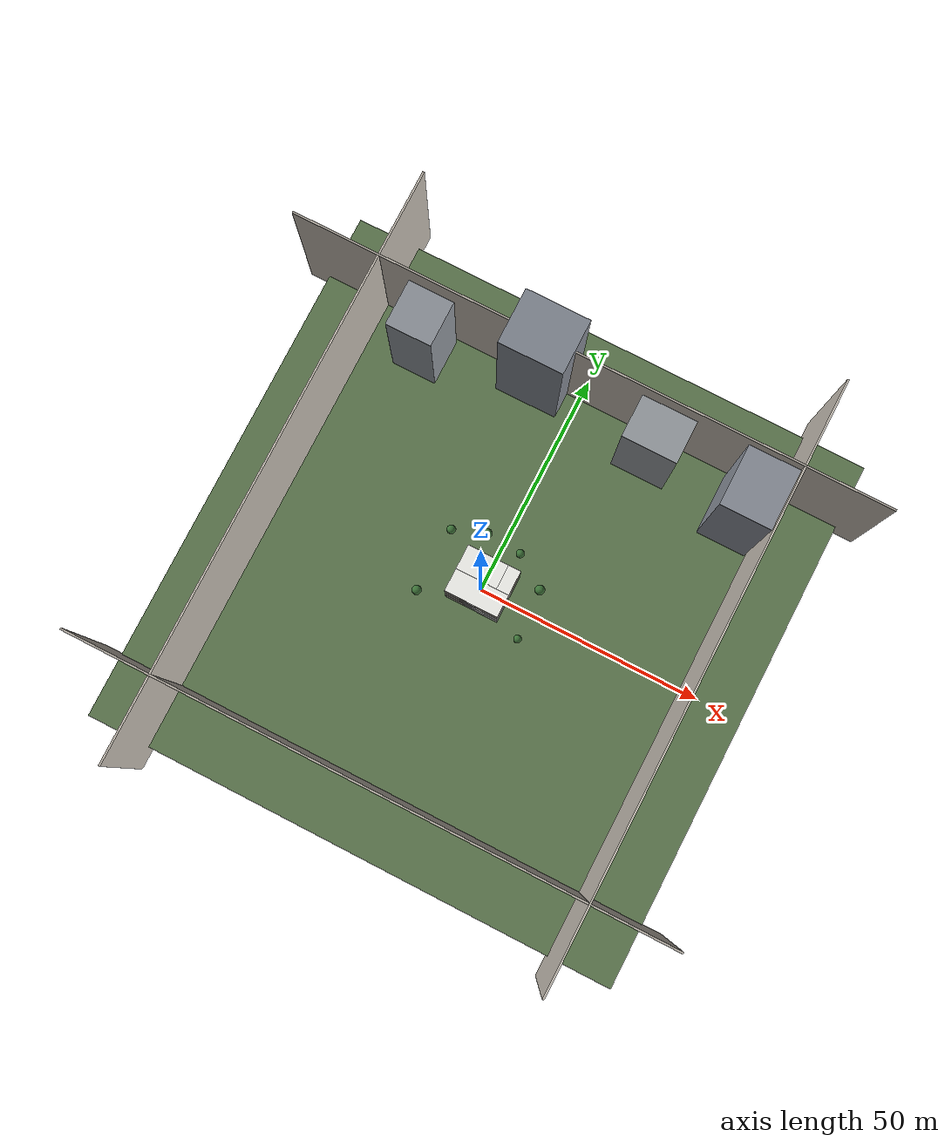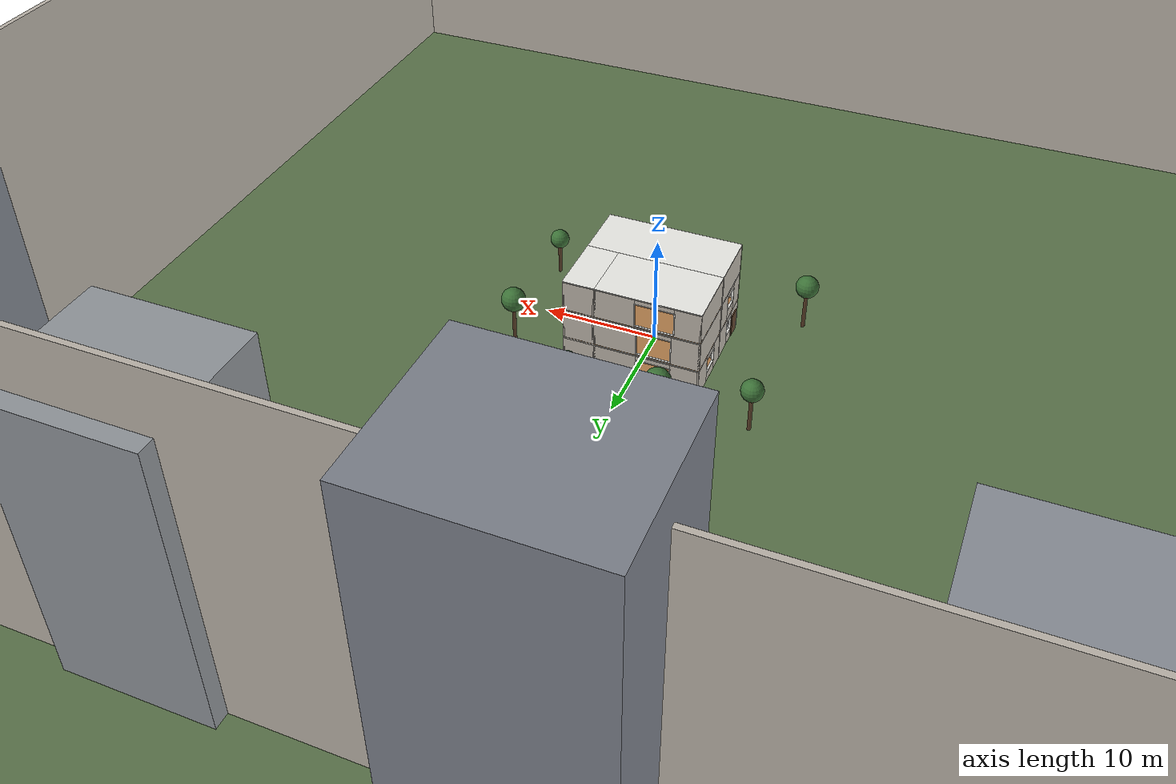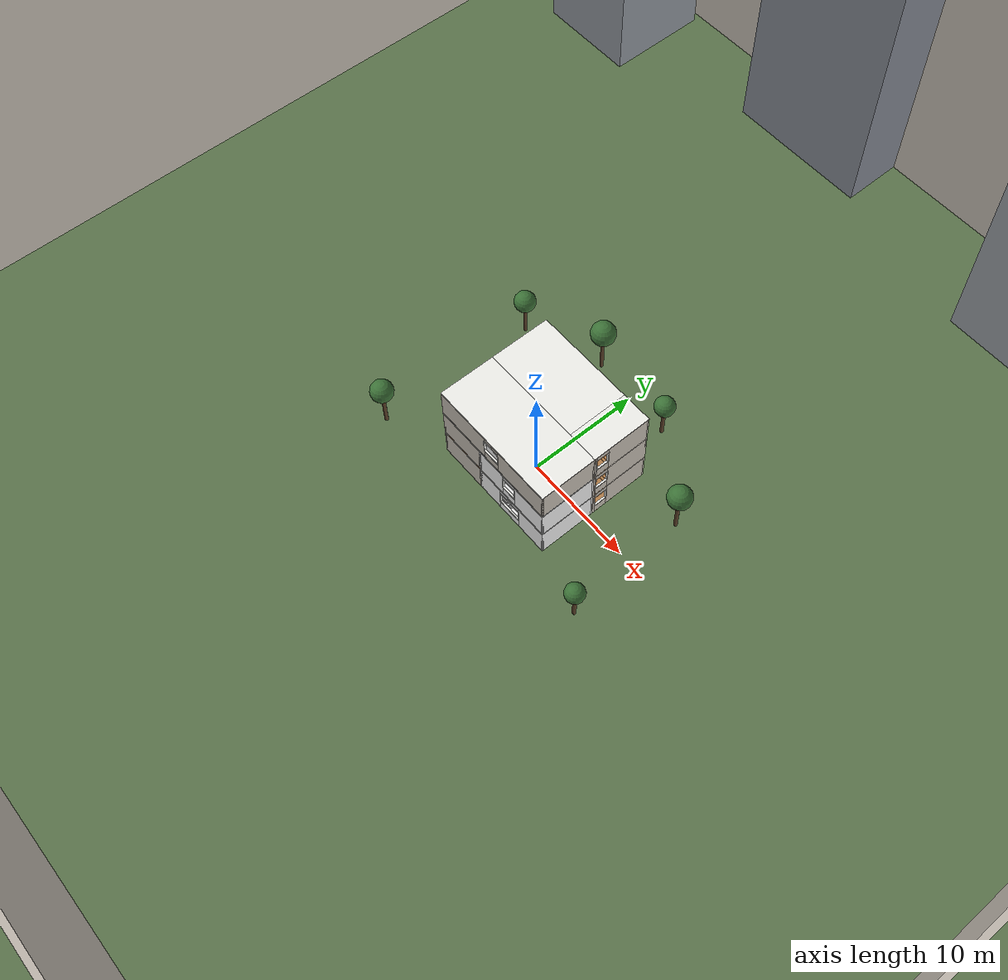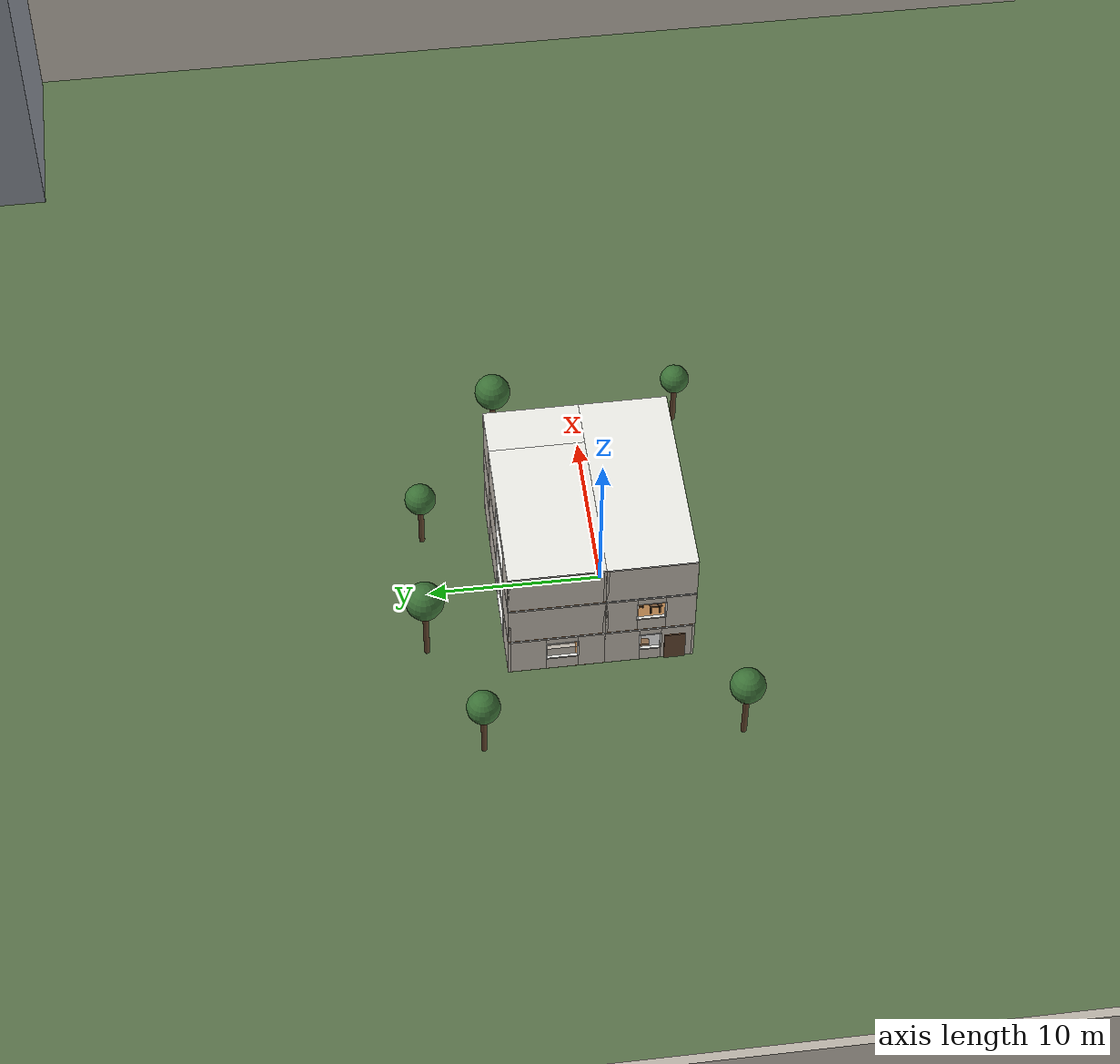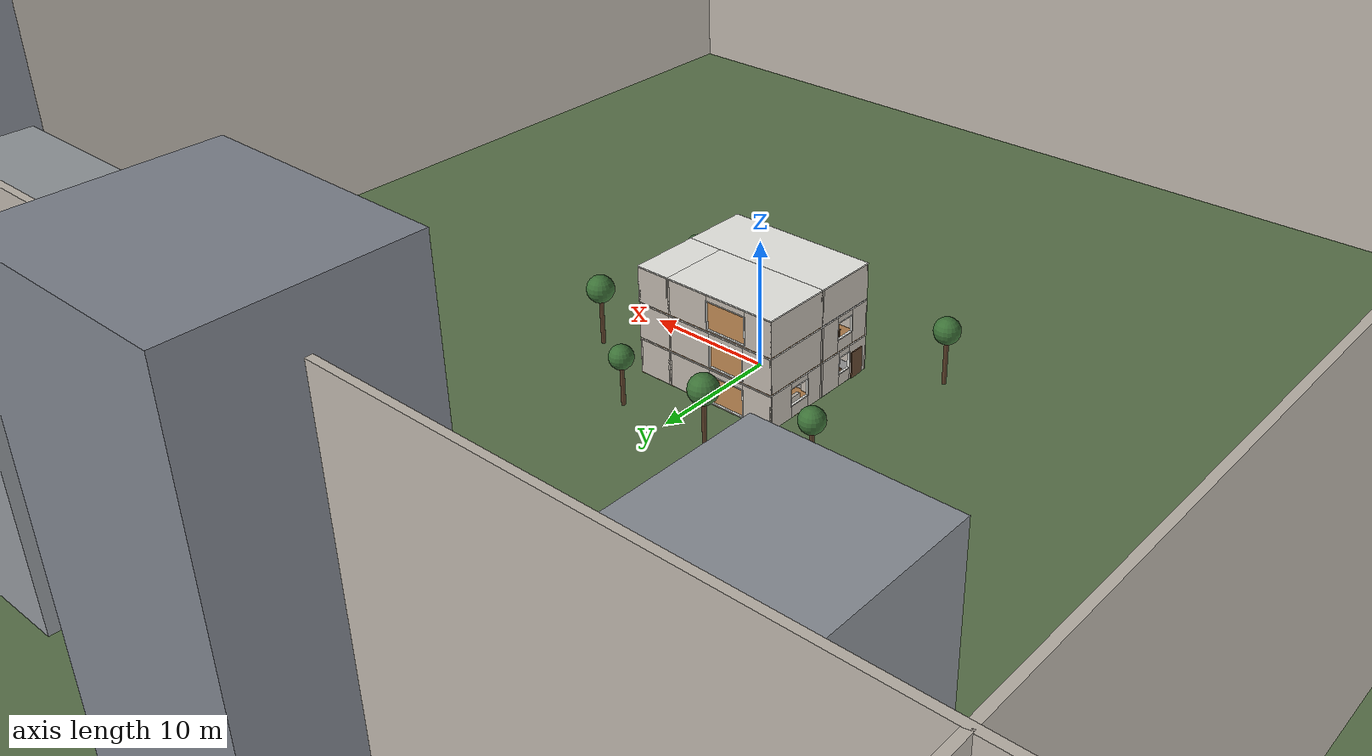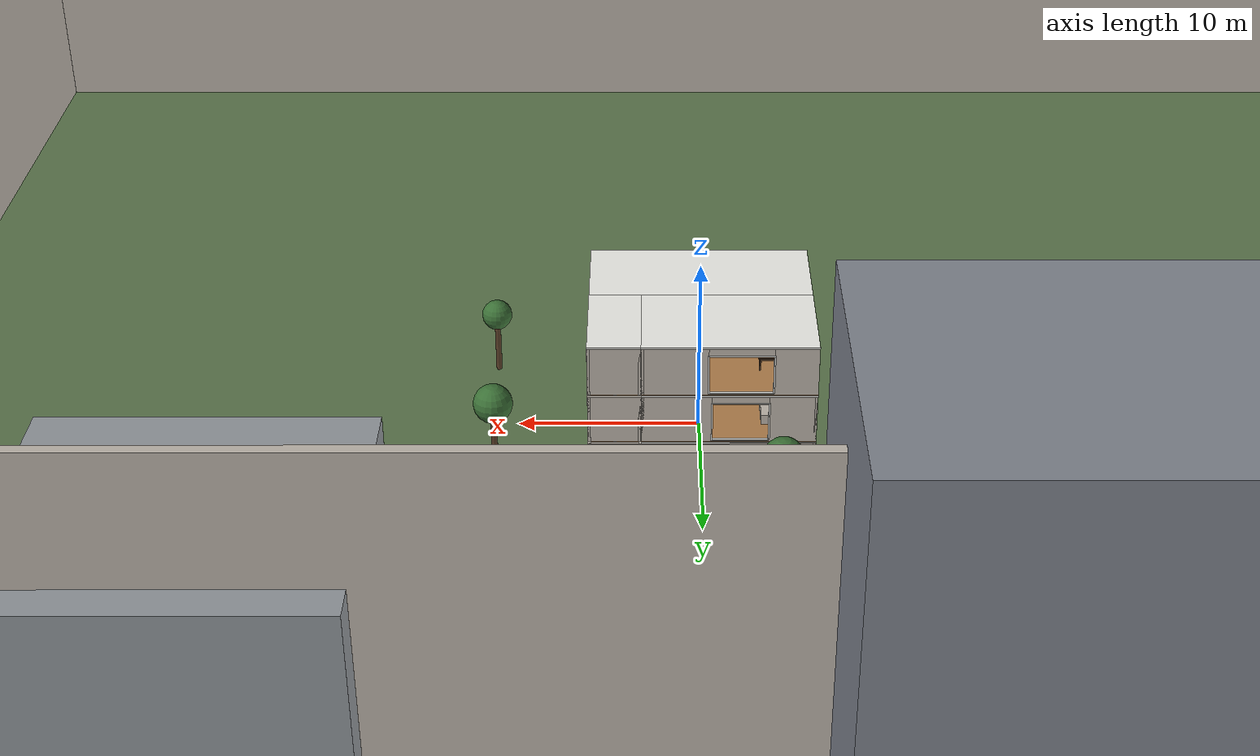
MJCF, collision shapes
<mujoco model="sim_house_nav_go2">
  <!-- 本文件由 make_house.py 从 layout.py 生成，请勿手改；改屋子改 layout.py 后重跑生成器。 -->
  <!-- 机器人：四足机器狗（宇树 Go2）（清单见 ../robots/manifest.py） -->
  <include file="robots/go2/go2.xml"/>

  <statistic center="0 -1 1" extent="6"/>

  <visual>
    <map znear="0.02" zfar="60"/>
    <headlight diffuse="0.45 0.45 0.45" ambient="0.34 0.34 0.34" specular="0.1 0.1 0.1"/>
    <quality shadowsize="4096"/>
    <global azimuth="120" elevation="-20" offwidth="1920" offheight="1080"/>
  </visual>

  <asset>
    <texture type="skybox" builtin="gradient" rgb1="0.52 0.68 0.88" rgb2="0.88 0.92 0.96" width="512" height="1024"/>
    <texture type="2d" name="tex_wood_floor" file="textures/wood_floor.png"/>
    <texture type="2d" name="tex_wood_floor_light" file="textures/wood_floor_light.png"/>
    <texture type="2d" name="tex_tile_white" file="textures/tile_white.png"/>
    <texture type="2d" name="tex_tile_grey" file="textures/tile_grey.png"/>
    <texture type="2d" name="tex_marble" file="textures/marble.png"/>
    <texture type="2d" name="tex_marble_dark" file="textures/marble_dark.png"/>
    <texture type="2d" name="tex_marble_warm" file="textures/marble_warm.png"/>
    <texture type="2d" name="tex_marble_grey" file="textures/marble_grey.png"/>
    <texture type="2d" name="tex_marble_greige" file="textures/marble_greige.png"/>
    <texture type="2d" name="tex_carpet" file="textures/carpet.png"/>
    <texture type="2d" name="tex_fabric" file="textures/fabric.png"/>
    <texture type="2d" name="tex_fabric_blue" file="textures/fabric_blue.png"/>
    <texture type="2d" name="tex_wall_paint" file="textures/wall_paint.png"/>
    <texture type="2d" name="tex_city_skyline" file="textures/city_skyline.png"/>
    <texture type="2d" name="tex_art0" file="textures/art0.png"/>
    <texture type="2d" name="tex_art1" file="textures/art1.png"/>
    <texture type="2d" name="tex_art2" file="textures/art2.png"/>
    <texture type="2d" name="tex_art3" file="textures/art3.png"/>
    <texture type="2d" name="tex_oven_glass" file="textures/oven_glass.png"/>
    <texture type="2d" name="tex_appliance_panel" file="textures/appliance_panel.png"/>
    <material name="mat_wood" texture="tex_wood_floor" texrepeat="3 3" specular="0.15" shininess="0.25" reflectance="0.02"/>
    <material name="mat_wood_light" texture="tex_wood_floor_light" texrepeat="3 3" specular="0.15" shininess="0.25" reflectance="0.02"/>
    <material name="mat_tile" texture="tex_tile_white" texrepeat="4 4" specular="0.35" shininess="0.55" reflectance="0.12"/>
    <material name="mat_tile_grey" texture="tex_tile_grey" texrepeat="4 4" specular="0.35" shininess="0.55" reflectance="0.12"/>
    <material name="mat_marble" texture="tex_marble" texrepeat="2 2" specular="0.45" shininess="0.7" reflectance="0.15"/>
    <material name="mat_marble_dark" texture="tex_marble_dark" texrepeat="2 2" specular="0.45" shininess="0.7" reflectance="0.15"/>
    <material name="mat_marble_warm" texture="tex_marble_warm" texrepeat="2 2" specular="0.45" shininess="0.7" reflectance="0.15"/>
    <material name="mat_marble_grey" texture="tex_marble_grey" texrepeat="2 2" specular="0.45" shininess="0.7" reflectance="0.15"/>
    <material name="mat_marble_greige" texture="tex_marble_greige" texrepeat="2 2" specular="0.2" shininess="0.35" reflectance="0.04"/>
    <material name="mat_carpet" texture="tex_carpet" texrepeat="4 4" specular="0.02" shininess="0.05" reflectance="0.0"/>
    <material name="mat_fabric" texture="tex_fabric" texrepeat="6 6" specular="0.05" shininess="0.1" reflectance="0.0"/>
    <material name="mat_fabric_blue" texture="tex_fabric_blue" texrepeat="6 6" specular="0.05" shininess="0.1" reflectance="0.0"/>
    <material name="mat_wall" texture="tex_wall_paint" texrepeat="2 2" specular="0.05" shininess="0.1" reflectance="0.0"/>
    <material name="mat_oven_glass" texture="tex_oven_glass" texrepeat="1 1" specular="0.85" shininess="0.9" reflectance="0.3"/>
    <material name="mat_appliance_panel" texture="tex_appliance_panel" texrepeat="1 1" specular="0.7" shininess="0.8" reflectance="0.25"/>
    <material name="mat_steel" rgba="0.82 0.84 0.87 1" specular="0.9" shininess="0.85" reflectance="0.35"/>
    <material name="mat_chrome" rgba="0.90 0.92 0.94 1" specular="1.0" shininess="0.95" reflectance="0.5"/>
    <material name="mat_glass" rgba="0.72 0.85 0.90 0.32" specular="0.8" shininess="0.9" reflectance="0.25"/>
    <material name="mat_porcelain" rgba="0.98 0.98 0.97 1" specular="0.55" shininess="0.75" reflectance="0.12"/>
    <material name="mat_screen" rgba="0.04 0.04 0.06 1" specular="0.6" shininess="0.9" reflectance="0.2"/>
    <material name="mat_city" texture="tex_city_skyline" specular="0" shininess="0" reflectance="0" emission="0.35"/>
    <material name="mat_art0" texture="tex_art0" specular="0.1" shininess="0.2"/>
    <material name="mat_art1" texture="tex_art1" specular="0.1" shininess="0.2"/>
    <material name="mat_art2" texture="tex_art2" specular="0.1" shininess="0.2"/>
    <material name="mat_art3" texture="tex_art3" specular="0.1" shininess="0.2"/>
    <material name="mat_mirror" rgba="0.78 0.85 0.90 1" specular="1.0" shininess="0.98" reflectance="0.6"/>
  </asset>

  <worldbody>
    <light name="light_entry" pos="-3.75 -1.95 2.58" dir="0 0 -1" diffuse="0.62 0.61 0.58" specular="0.05 0.05 0.05" attenuation="0.55 0.06 0.010"/>
    <light name="light_living_room" pos="-1.4 3.34 2.58" dir="0 0 -1" diffuse="0.62 0.61 0.58" specular="0.05 0.05 0.05" attenuation="0.55 0.06 0.010"/>
    <light name="light_kitchen" pos="2.25 -1.95 2.58" dir="0 0 -1" diffuse="0.62 0.61 0.58" specular="0.05 0.05 0.05" attenuation="0.55 0.06 0.010"/>
    <light name="light_stair_f0" pos="4.6 3.34 2.58" dir="0 0 -1" diffuse="0.62 0.61 0.58" specular="0.05 0.05 0.05" attenuation="0.55 0.06 0.010"/>
    <light name="light_study" pos="-3.75 -1.95 5.46" dir="0 0 -1" diffuse="0.62 0.61 0.58" specular="0.05 0.05 0.05" attenuation="0.55 0.06 0.010"/>
    <light name="light_bedroom" pos="-1.4 3.34 5.46" dir="0 0 -1" diffuse="0.62 0.61 0.58" specular="0.05 0.05 0.05" attenuation="0.55 0.06 0.010"/>
    <light name="light_bathroom" pos="2.25 -1.95 5.46" dir="0 0 -1" diffuse="0.62 0.61 0.58" specular="0.05 0.05 0.05" attenuation="0.55 0.06 0.010"/>
    <light name="light_stair_f1" pos="4.6 3.34 5.46" dir="0 0 -1" diffuse="0.62 0.61 0.58" specular="0.05 0.05 0.05" attenuation="0.55 0.06 0.010"/>
    <light name="light_storage" pos="0 -1.95 8.34" dir="0 0 -1" diffuse="0.62 0.61 0.58" specular="0.05 0.05 0.05" attenuation="0.55 0.06 0.010"/>
    <light name="light_studio" pos="-1.4 3.34 8.34" dir="0 0 -1" diffuse="0.62 0.61 0.58" specular="0.05 0.05 0.05" attenuation="0.55 0.06 0.010"/>
    <light name="light_stair_f2" pos="4.6 3.34 8.34" dir="0 0 -1" diffuse="0.62 0.61 0.58" specular="0.05 0.05 0.05" attenuation="0.55 0.06 0.010"/>
    <light name="sun" pos="10 -18 22" dir="-0.35 0.62 -0.70" directional="true" diffuse="0.55 0.54 0.50" specular="0.10 0.10 0.10"/>

    <!-- ===== 门厅 ===== -->
    <geom name="entry_floor" type="box" size="2.25 2.55 0.025" pos="-3.75 -1.95 -0.025" material="mat_marble_grey"/>
    <geom name="entry_ceiling" type="box" size="2.25 2.55 0.05" pos="-3.75 -1.95 2.78" rgba="0.95 0.95 0.93 1" group="1"/>
    <geom name="entry_ws0" type="box" size="2.25 0.07 1.365" pos="-3.75 -4.43 1.365" material="mat_wall"/>
    <geom name="entry_wn0" type="box" size="0.85 0.07 1.365" pos="-5.15 0.53 1.365" material="mat_wall"/>
    <geom name="entry_wn1" type="box" size="0.6 0.07 1.365" pos="-2.1 0.53 1.365" material="mat_wall"/>
    <geom name="entry_ww0" type="box" size="0.07 0.95 1.365" pos="-5.93 -3.55 1.365" material="mat_wall"/>
    <geom name="entry_ww1" type="box" size="0.07 1 1.365" pos="-5.93 -0.4 1.365" material="mat_wall"/>
    <geom name="entry_ww2" type="box" size="0.07 0.6 0.475" pos="-5.93 -2 0.475" material="mat_wall"/>
    <geom name="entry_ww3" type="box" size="0.07 0.6 0.215" pos="-5.93 -2 2.515" material="mat_wall"/>
    <geom name="entry_wfw0_l" type="box" size="0.085 0.04 0.675" pos="-5.93 -2.6 1.625" rgba="0.93 0.93 0.91 1"/>
    <geom name="entry_wfw0_r" type="box" size="0.085 0.04 0.675" pos="-5.93 -1.4 1.625" rgba="0.93 0.93 0.91 1"/>
    <geom name="entry_wfw0_top" type="box" size="0.085 0.64 0.04" pos="-5.93 -2 2.3" rgba="0.93 0.93 0.91 1"/>
    <geom name="entry_wfw0_bot" type="box" size="0.085 0.64 0.04" pos="-5.93 -2 0.95" rgba="0.93 0.93 0.91 1"/>
    <geom name="entry_we0" type="box" size="0.07 0.925 1.365" pos="-1.57 -3.575 1.365" material="mat_wall"/>
    <geom name="entry_we1" type="box" size="0.07 0.975 1.365" pos="-1.57 -0.375 1.365" material="mat_wall"/>
    <geom name="entry_we2" type="box" size="0.07 0.65 0.315" pos="-1.57 -2 2.415" material="mat_wall"/>
    <geom name="entry_we3" type="box" size="0.07 0.65 0.315" pos="-1.57 -2 2.415" material="mat_wall"/>
    <geom name="entry_dfe0_l" type="box" size="0.085 0.05 1.05" pos="-1.57 -2.65 1.05" rgba="0.4 0.29 0.2 1"/>
    <geom name="entry_dfe0_r" type="box" size="0.085 0.05 1.05" pos="-1.57 -1.35 1.05" rgba="0.4 0.29 0.2 1"/>
    <geom name="entry_dfe0_top" type="box" size="0.085 0.7 0.05" pos="-1.57 -2 2.1" rgba="0.4 0.29 0.2 1"/>
    <geom name="entry_dfe1_l" type="box" size="0.085 0.05 1.05" pos="-1.57 -2.65 1.05" rgba="0.4 0.29 0.2 1"/>
    <geom name="entry_dfe1_r" type="box" size="0.085 0.05 1.05" pos="-1.57 -1.35 1.05" rgba="0.4 0.29 0.2 1"/>
    <geom name="entry_dfe1_top" type="box" size="0.085 0.7 0.05" pos="-1.57 -2 2.1" rgba="0.4 0.29 0.2 1"/>
    <geom name="furn_h2_shoe_cab" type="box" size="0.19 0.8 0.55" pos="-5.6 -1.2 0.55" rgba="0.55 0.42 0.3 1"/>

    <!-- ===== 客厅 ===== -->
    <geom name="living_room_floor" type="box" size="4.6 2.74 0.025" pos="-1.4 3.34 -0.025" material="mat_wood_light"/>
    <geom name="living_room_ceiling" type="box" size="4.6 2.74 0.05" pos="-1.4 3.34 2.78" rgba="0.95 0.95 0.93 1" group="1"/>
    <geom name="living_room_ws0" type="box" size="0.85 0.07 1.365" pos="-5.15 0.67 1.365" material="mat_wall"/>
    <geom name="living_room_ws1" type="box" size="2.95 0.07 1.365" pos="0.25 0.67 1.365" material="mat_wall"/>
    <geom name="living_room_wn0" type="box" size="1.25 0.07 1.365" pos="-4.75 6.01 1.365" material="mat_wall"/>
    <geom name="living_room_wn1" type="box" size="1.85 0.07 1.365" pos="1.35 6.01 1.365" material="mat_wall"/>
    <geom name="living_room_wn2" type="box" size="1.5 0.07 0.03" pos="-2 6.01 0.03" material="mat_wall"/>
    <geom name="living_room_wn3" type="box" size="1.5 0.07 0.215" pos="-2 6.01 2.515" material="mat_wall"/>
    <geom name="living_room_wfn0_l" type="box" size="0.04 0.085 1.12" pos="-3.5 6.01 1.18" rgba="0.93 0.93 0.91 1"/>
    <geom name="living_room_wfn0_r" type="box" size="0.04 0.085 1.12" pos="-0.5 6.01 1.18" rgba="0.93 0.93 0.91 1"/>
    <geom name="living_room_wfn0_top" type="box" size="1.54 0.085 0.04" pos="-2 6.01 2.3" rgba="0.93 0.93 0.91 1"/>
    <geom name="living_room_wfn0_bot" type="box" size="1.54 0.085 0.04" pos="-2 6.01 0.06" rgba="0.93 0.93 0.91 1"/>
    <geom name="living_room_ww0" type="box" size="0.07 0.75 1.365" pos="-5.93 1.35 1.365" material="mat_wall"/>
    <geom name="living_room_ww1" type="box" size="0.07 1.09 1.365" pos="-5.93 4.99 1.365" material="mat_wall"/>
    <geom name="living_room_ww2" type="box" size="0.07 0.9 0.475" pos="-5.93 3 0.475" material="mat_wall"/>
    <geom name="living_room_ww3" type="box" size="0.07 0.9 0.215" pos="-5.93 3 2.515" material="mat_wall"/>
    <geom name="living_room_wfw0_l" type="box" size="0.085 0.04 0.675" pos="-5.93 2.1 1.625" rgba="0.93 0.93 0.91 1"/>
    <geom name="living_room_wfw0_r" type="box" size="0.085 0.04 0.675" pos="-5.93 3.9 1.625" rgba="0.93 0.93 0.91 1"/>
    <geom name="living_room_wfw0_top" type="box" size="0.085 0.94 0.04" pos="-5.93 3 2.3" rgba="0.93 0.93 0.91 1"/>
    <geom name="living_room_wfw0_bot" type="box" size="0.085 0.94 0.04" pos="-5.93 3 0.95" rgba="0.93 0.93 0.91 1"/>
    <geom name="living_room_we0" type="box" size="0.07 2.74 1.365" pos="3.13 3.34 1.365" material="mat_wall"/>
    <geom name="furn_h2_sofa_seat" type="box" size="0.475 1.2 0.22" pos="-4.6 3.34 0.22" material="mat_fabric"/>
    <geom name="furn_h2_sofa_back" type="box" size="0.125 1.2 0.33" pos="-5.2 3.34 0.55" material="mat_fabric"/>
    <geom name="furn_h2_tv_console" type="box" size="0.21 1.1 0.26" pos="2.5 3.34 0.26" rgba="0.55 0.42 0.3 1"/>
    <geom name="furn_h2_tv_screen" type="box" size="0.03 0.8 0.46" pos="2.95 3.34 1.25" material="mat_screen"/>
    <geom name="furn_h2_coffee_top" type="cylinder" size="0.525 0.035" pos="-3 3.34 0.4" rgba="0.46 0.33 0.22 1"/>
    <geom name="furn_h2_coffee_neck" type="cylinder" size="0.28875 0.03" pos="-3 3.34 0.3" rgba="0.46 0.33 0.22 1"/>
    <geom name="furn_h2_coffee_post" type="cylinder" size="0.1155 0.12" pos="-3 3.34 0.17" rgba="0.34 0.24 0.16 1"/>
    <geom name="furn_h2_coffee_footring" type="cylinder" size="0.3255 0.025" pos="-3 3.34 0.05" rgba="0.34 0.24 0.16 1"/>
    <geom name="furn_h2_coffee_footpad" type="cylinder" size="0.357 0.015" pos="-3 3.34 0.015" rgba="0.34 0.24 0.16 1"/>
    <geom name="furn_h2_flamp_base" type="cylinder" size="0.17 0.018" pos="-5.4 5.34 0.018" rgba="0.2 0.2 0.22 1"/>
    <geom name="furn_h2_flamp_base2" type="cylinder" size="0.11 0.02" pos="-5.4 5.34 0.055" rgba="0.26 0.26 0.28 1"/>
    <geom name="furn_h2_flamp_pole" type="cylinder" size="0.0225 0.81" pos="-5.4 5.34 0.81" rgba="0.42 0.43 0.46 1"/>
    <geom name="furn_h2_flamp_collar" type="cylinder" size="0.045 0.025" pos="-5.4 5.34 1.32" rgba="0.3 0.3 0.32 1"/>
    <geom name="furn_h2_flamp_shade" type="cylinder" size="0.21 0.15" pos="-5.4 5.34 1.56" rgba="0.97 0.93 0.76 1"/>
    <geom name="furn_h2_flamp_shade_top" type="cylinder" size="0.1512 0.015" pos="-5.4 5.34 1.72" rgba="0.9 0.86 0.7 1"/>
    <geom name="furn_h2_plant_lr_pot" type="cylinder" size="0.23 0.2" pos="2.56 5.44 0.2" rgba="0.52 0.4 0.33 1"/>
    <geom name="furn_h2_plant_lr_pot_rim" type="cylinder" size="0.2484 0.025" pos="2.56 5.44 0.41" rgba="0.46 0.35 0.29 1"/>
    <geom name="furn_h2_plant_lr_soil" type="cylinder" size="0.207 0.015" pos="2.56 5.44 0.43" rgba="0.22 0.17 0.13 1"/>
    <geom name="furn_h2_plant_lr_trunk" type="cylinder" size="0.035 0.18" pos="2.56 5.44 0.62" rgba="0.34 0.26 0.18 1"/>
    <geom name="furn_h2_plant_lr_leaf_a" type="sphere" size="0.31" pos="2.56 5.44 1.05" rgba="0.24 0.46 0.26 1"/>
    <geom name="furn_h2_plant_lr_leaf_b" type="sphere" size="0.22" pos="2.76 5.32 0.89" rgba="0.28 0.52 0.3 1"/>
    <geom name="furn_h2_plant_lr_leaf_c" type="sphere" size="0.2" pos="2.38 5.58 0.85" rgba="0.22 0.43 0.24 1"/>

    <!-- ===== 厨房 ===== -->
    <geom name="kitchen_floor" type="box" size="3.75 2.55 0.025" pos="2.25 -1.95 -0.025" material="mat_tile"/>
    <geom name="kitchen_ceiling" type="box" size="3.75 2.55 0.05" pos="2.25 -1.95 2.78" rgba="0.95 0.95 0.93 1" group="1"/>
    <geom name="kitchen_ws0" type="box" size="1.2 0.07 1.365" pos="-0.3 -4.43 1.365" material="mat_tile"/>
    <geom name="kitchen_ws1" type="box" size="1.45 0.07 1.365" pos="4.55 -4.43 1.365" material="mat_tile"/>
    <geom name="kitchen_ws2" type="box" size="1.1 0.07 0.475" pos="2 -4.43 0.475" material="mat_tile"/>
    <geom name="kitchen_ws3" type="box" size="1.1 0.07 0.215" pos="2 -4.43 2.515" material="mat_tile"/>
    <geom name="kitchen_wfs0_l" type="box" size="0.04 0.085 0.675" pos="0.9 -4.43 1.625" rgba="0.93 0.93 0.91 1"/>
    <geom name="kitchen_wfs0_r" type="box" size="0.04 0.085 0.675" pos="3.1 -4.43 1.625" rgba="0.93 0.93 0.91 1"/>
    <geom name="kitchen_wfs0_top" type="box" size="1.14 0.085 0.04" pos="2 -4.43 2.3" rgba="0.93 0.93 0.91 1"/>
    <geom name="kitchen_wfs0_bot" type="box" size="1.14 0.085 0.04" pos="2 -4.43 0.95" rgba="0.93 0.93 0.91 1"/>
    <geom name="kitchen_wn0" type="box" size="2.75 0.07 1.365" pos="1.25 0.53 1.365" material="mat_tile"/>
    <geom name="kitchen_wn1" type="box" size="0.4 0.07 1.365" pos="5.6 0.53 1.365" material="mat_tile"/>
    <geom name="kitchen_ww0" type="box" size="0.07 0.925 1.365" pos="-1.43 -3.575 1.365" material="mat_tile"/>
    <geom name="kitchen_ww1" type="box" size="0.07 0.975 1.365" pos="-1.43 -0.375 1.365" material="mat_tile"/>
    <geom name="kitchen_ww2" type="box" size="0.07 0.65 0.315" pos="-1.43 -2 2.415" material="mat_tile"/>
    <geom name="kitchen_ww3" type="box" size="0.07 0.65 0.315" pos="-1.43 -2 2.415" material="mat_tile"/>
    <geom name="kitchen_dfw0_l" type="box" size="0.085 0.05 1.05" pos="-1.43 -2.65 1.05" rgba="0.4 0.29 0.2 1"/>
    <geom name="kitchen_dfw0_r" type="box" size="0.085 0.05 1.05" pos="-1.43 -1.35 1.05" rgba="0.4 0.29 0.2 1"/>
    <geom name="kitchen_dfw0_top" type="box" size="0.085 0.7 0.05" pos="-1.43 -2 2.1" rgba="0.4 0.29 0.2 1"/>
    <geom name="kitchen_dfw1_l" type="box" size="0.085 0.05 1.05" pos="-1.43 -2.65 1.05" rgba="0.4 0.29 0.2 1"/>
    <geom name="kitchen_dfw1_r" type="box" size="0.085 0.05 1.05" pos="-1.43 -1.35 1.05" rgba="0.4 0.29 0.2 1"/>
    <geom name="kitchen_dfw1_top" type="box" size="0.085 0.7 0.05" pos="-1.43 -2 2.1" rgba="0.4 0.29 0.2 1"/>
    <geom name="kitchen_we0" type="box" size="0.07 2.55 1.365" pos="5.93 -1.95 1.365" material="mat_tile"/>
    <geom name="furn_h2_counter" type="box" size="1.4 0.31 0.45" pos="0.2 -4.1 0.45" material="mat_marble_grey"/>
    <geom name="furn_h2_upper_cab" type="box" size="1.4 0.18 0.35" pos="0.2 -4.2 1.75" rgba="0.9 0.9 0.88 1"/>
    <geom name="furn_h2_dining_top" type="box" size="0.7 0.45 0.03" pos="3.2 -2.2 0.75" rgba="0.46 0.33 0.22 1"/>
    <geom name="furn_h2_dining_apron_n" type="box" size="0.62 0.02 0.05" pos="3.2 -1.81 0.66" rgba="0.34 0.24 0.16 1"/>
    <geom name="furn_h2_dining_apron_s" type="box" size="0.62 0.02 0.05" pos="3.2 -2.59 0.66" rgba="0.34 0.24 0.16 1"/>
    <geom name="furn_h2_dining_apron_e" type="box" size="0.02 0.37 0.05" pos="3.84 -2.2 0.66" rgba="0.34 0.24 0.16 1"/>
    <geom name="furn_h2_dining_apron_w" type="box" size="0.02 0.37 0.05" pos="2.56 -2.2 0.66" rgba="0.34 0.24 0.16 1"/>
    <geom name="furn_h2_dining_lega" type="box" size="0.04 0.04 0.36" pos="3.8 -1.85 0.36" rgba="0.34 0.24 0.16 1"/>
    <geom name="furn_h2_dining_legb" type="box" size="0.04 0.04 0.36" pos="3.8 -2.55 0.36" rgba="0.34 0.24 0.16 1"/>
    <geom name="furn_h2_dining_legc" type="box" size="0.04 0.04 0.36" pos="2.6 -1.85 0.36" rgba="0.34 0.24 0.16 1"/>
    <geom name="furn_h2_dining_legd" type="box" size="0.04 0.04 0.36" pos="2.6 -2.55 0.36" rgba="0.34 0.24 0.16 1"/>
    <geom name="furn_h2_dc_n1_seat" type="box" size="0.23 0.23 0.03" pos="2.75 -1.45 0.45" quat="0.707107 0 0 -0.707107" rgba="0.46 0.33 0.22 1"/>
    <geom name="furn_h2_dc_n1_back" type="box" size="0.03 0.2185 0.26" pos="2.75 -1.26 0.71" quat="0.707107 0 0 -0.707107" rgba="0.46 0.33 0.22 1"/>
    <geom name="furn_h2_dc_n1_slata" type="box" size="0.035 0.025 0.2548" pos="2.6212 -1.26 0.71" quat="0.707107 0 0 -0.707107" rgba="0.34 0.24 0.16 1"/>
    <geom name="furn_h2_dc_n1_slatb" type="box" size="0.035 0.025 0.2548" pos="2.8788 -1.26 0.71" quat="0.707107 0 0 -0.707107" rgba="0.34 0.24 0.16 1"/>
    <geom name="furn_h2_dc_n1_legfl" type="box" size="0.025 0.025 0.21" pos="2.925 -1.625 0.21" quat="0.707107 0 0 -0.707107" rgba="0.34 0.24 0.16 1"/>
    <geom name="furn_h2_dc_n1_legfr" type="box" size="0.025 0.025 0.21" pos="2.575 -1.625 0.21" quat="0.707107 0 0 -0.707107" rgba="0.34 0.24 0.16 1"/>
    <geom name="furn_h2_dc_n1_legrl" type="box" size="0.025 0.025 0.21" pos="2.925 -1.275 0.21" quat="0.707107 0 0 -0.707107" rgba="0.34 0.24 0.16 1"/>
    <geom name="furn_h2_dc_n1_legrr" type="box" size="0.025 0.025 0.21" pos="2.575 -1.275 0.21" quat="0.707107 0 0 -0.707107" rgba="0.34 0.24 0.16 1"/>
    <geom name="furn_h2_dc_n1_railf" type="box" size="0.02 0.175 0.02" pos="2.75 -1.625 0.153" quat="0.707107 0 0 -0.707107" rgba="0.34 0.24 0.16 1"/>
    <geom name="furn_h2_dc_n1_railr" type="box" size="0.02 0.175 0.02" pos="2.75 -1.275 0.153" quat="0.707107 0 0 -0.707107" rgba="0.34 0.24 0.16 1"/>
    <geom name="furn_h2_dc_n2_seat" type="box" size="0.23 0.23 0.03" pos="3.65 -1.45 0.45" quat="0.707107 0 0 -0.707107" rgba="0.46 0.33 0.22 1"/>
    <geom name="furn_h2_dc_n2_back" type="box" size="0.03 0.2185 0.26" pos="3.65 -1.26 0.71" quat="0.707107 0 0 -0.707107" rgba="0.46 0.33 0.22 1"/>
    <geom name="furn_h2_dc_n2_slata" type="box" size="0.035 0.025 0.2548" pos="3.5212 -1.26 0.71" quat="0.707107 0 0 -0.707107" rgba="0.34 0.24 0.16 1"/>
    <geom name="furn_h2_dc_n2_slatb" type="box" size="0.035 0.025 0.2548" pos="3.7788 -1.26 0.71" quat="0.707107 0 0 -0.707107" rgba="0.34 0.24 0.16 1"/>
    <geom name="furn_h2_dc_n2_legfl" type="box" size="0.025 0.025 0.21" pos="3.825 -1.625 0.21" quat="0.707107 0 0 -0.707107" rgba="0.34 0.24 0.16 1"/>
    <geom name="furn_h2_dc_n2_legfr" type="box" size="0.025 0.025 0.21" pos="3.475 -1.625 0.21" quat="0.707107 0 0 -0.707107" rgba="0.34 0.24 0.16 1"/>
    <geom name="furn_h2_dc_n2_legrl" type="box" size="0.025 0.025 0.21" pos="3.825 -1.275 0.21" quat="0.707107 0 0 -0.707107" rgba="0.34 0.24 0.16 1"/>
    <geom name="furn_h2_dc_n2_legrr" type="box" size="0.025 0.025 0.21" pos="3.475 -1.275 0.21" quat="0.707107 0 0 -0.707107" rgba="0.34 0.24 0.16 1"/>
    <geom name="furn_h2_dc_n2_railf" type="box" size="0.02 0.175 0.02" pos="3.65 -1.625 0.153" quat="0.707107 0 0 -0.707107" rgba="0.34 0.24 0.16 1"/>
    <geom name="furn_h2_dc_n2_railr" type="box" size="0.02 0.175 0.02" pos="3.65 -1.275 0.153" quat="0.707107 0 0 -0.707107" rgba="0.34 0.24 0.16 1"/>
    <geom name="furn_h2_dc_s1_seat" type="box" size="0.23 0.23 0.03" pos="2.75 -2.95 0.45" quat="0.707107 0 0 0.707107" rgba="0.46 0.33 0.22 1"/>
    <geom name="furn_h2_dc_s1_back" type="box" size="0.03 0.2185 0.26" pos="2.75 -3.14 0.71" quat="0.707107 0 0 0.707107" rgba="0.46 0.33 0.22 1"/>
    <geom name="furn_h2_dc_s1_slata" type="box" size="0.035 0.025 0.2548" pos="2.8788 -3.14 0.71" quat="0.707107 0 0 0.707107" rgba="0.34 0.24 0.16 1"/>
    <geom name="furn_h2_dc_s1_slatb" type="box" size="0.035 0.025 0.2548" pos="2.6212 -3.14 0.71" quat="0.707107 0 0 0.707107" rgba="0.34 0.24 0.16 1"/>
    <geom name="furn_h2_dc_s1_legfl" type="box" size="0.025 0.025 0.21" pos="2.575 -2.775 0.21" quat="0.707107 0 0 0.707107" rgba="0.34 0.24 0.16 1"/>
    <geom name="furn_h2_dc_s1_legfr" type="box" size="0.025 0.025 0.21" pos="2.925 -2.775 0.21" quat="0.707107 0 0 0.707107" rgba="0.34 0.24 0.16 1"/>
    <geom name="furn_h2_dc_s1_legrl" type="box" size="0.025 0.025 0.21" pos="2.575 -3.125 0.21" quat="0.707107 0 0 0.707107" rgba="0.34 0.24 0.16 1"/>
    <geom name="furn_h2_dc_s1_legrr" type="box" size="0.025 0.025 0.21" pos="2.925 -3.125 0.21" quat="0.707107 0 0 0.707107" rgba="0.34 0.24 0.16 1"/>
    <geom name="furn_h2_dc_s1_railf" type="box" size="0.02 0.175 0.02" pos="2.75 -2.775 0.153" quat="0.707107 0 0 0.707107" rgba="0.34 0.24 0.16 1"/>
    <geom name="furn_h2_dc_s1_railr" type="box" size="0.02 0.175 0.02" pos="2.75 -3.125 0.153" quat="0.707107 0 0 0.707107" rgba="0.34 0.24 0.16 1"/>
    <geom name="furn_h2_dc_s2_seat" type="box" size="0.23 0.23 0.03" pos="3.65 -2.95 0.45" quat="0.707107 0 0 0.707107" rgba="0.46 0.33 0.22 1"/>
    <geom name="furn_h2_dc_s2_back" type="box" size="0.03 0.2185 0.26" pos="3.65 -3.14 0.71" quat="0.707107 0 0 0.707107" rgba="0.46 0.33 0.22 1"/>
    <geom name="furn_h2_dc_s2_slata" type="box" size="0.035 0.025 0.2548" pos="3.7788 -3.14 0.71" quat="0.707107 0 0 0.707107" rgba="0.34 0.24 0.16 1"/>
    <geom name="furn_h2_dc_s2_slatb" type="box" size="0.035 0.025 0.2548" pos="3.5212 -3.14 0.71" quat="0.707107 0 0 0.707107" rgba="0.34 0.24 0.16 1"/>
    <geom name="furn_h2_dc_s2_legfl" type="box" size="0.025 0.025 0.21" pos="3.475 -2.775 0.21" quat="0.707107 0 0 0.707107" rgba="0.34 0.24 0.16 1"/>
    <geom name="furn_h2_dc_s2_legfr" type="box" size="0.025 0.025 0.21" pos="3.825 -2.775 0.21" quat="0.707107 0 0 0.707107" rgba="0.34 0.24 0.16 1"/>
    <geom name="furn_h2_dc_s2_legrl" type="box" size="0.025 0.025 0.21" pos="3.475 -3.125 0.21" quat="0.707107 0 0 0.707107" rgba="0.34 0.24 0.16 1"/>
    <geom name="furn_h2_dc_s2_legrr" type="box" size="0.025 0.025 0.21" pos="3.825 -3.125 0.21" quat="0.707107 0 0 0.707107" rgba="0.34 0.24 0.16 1"/>
    <geom name="furn_h2_dc_s2_railf" type="box" size="0.02 0.175 0.02" pos="3.65 -2.775 0.153" quat="0.707107 0 0 0.707107" rgba="0.34 0.24 0.16 1"/>
    <geom name="furn_h2_dc_s2_railr" type="box" size="0.02 0.175 0.02" pos="3.65 -3.125 0.153" quat="0.707107 0 0 0.707107" rgba="0.34 0.24 0.16 1"/>

    <!-- ===== 楼梯间 ===== -->
    <geom name="stair_f0_floor" type="box" size="1.4 2.74 0.025" pos="4.6 3.34 -0.025" material="mat_wood_light"/>
    <geom name="stair_f0_ws0" type="box" size="0.4 0.07 1.365" pos="3.6 0.67 1.365" material="mat_wall"/>
    <geom name="stair_f0_ws1" type="box" size="0.4 0.07 1.365" pos="5.6 0.67 1.365" material="mat_wall"/>
    <geom name="stair_f0_wn0" type="box" size="1.4 0.07 1.365" pos="4.6 6.01 1.365" material="mat_wall"/>
    <geom name="stair_f0_ww0" type="box" size="0.07 2.74 1.365" pos="3.27 3.34 1.365" material="mat_wall"/>
    <geom name="stair_f0_we0" type="box" size="0.07 0.12 1.365" pos="5.93 0.72 1.365" material="mat_wall"/>
    <geom name="stair_f0_we1" type="box" size="0.07 2.02 1.365" pos="5.93 4.06 1.365" material="mat_wall"/>
    <geom name="stair_f0_we2" type="box" size="0.07 0.6 0.475" pos="5.93 1.44 0.475" material="mat_wall"/>
    <geom name="stair_f0_we3" type="box" size="0.07 0.6 0.215" pos="5.93 1.44 2.515" material="mat_wall"/>
    <geom name="stair_f0_wfe0_l" type="box" size="0.085 0.04 0.675" pos="5.93 0.84 1.625" rgba="0.93 0.93 0.91 1"/>
    <geom name="stair_f0_wfe0_r" type="box" size="0.085 0.04 0.675" pos="5.93 2.04 1.625" rgba="0.93 0.93 0.91 1"/>
    <geom name="stair_f0_wfe0_top" type="box" size="0.085 0.64 0.04" pos="5.93 1.44 2.3" rgba="0.93 0.93 0.91 1"/>
    <geom name="stair_f0_wfe0_bot" type="box" size="0.085 0.64 0.04" pos="5.93 1.44 0.95" rgba="0.93 0.93 0.91 1"/>

    <!-- ===== 书房 ===== -->
    <geom name="study_floor" type="box" size="2.25 2.55 0.025" pos="-3.75 -1.95 2.855" material="mat_wood_light"/>
    <geom name="study_ceiling" type="box" size="2.25 2.55 0.05" pos="-3.75 -1.95 5.66" rgba="0.95 0.95 0.93 1" group="1"/>
    <geom name="study_ws0" type="box" size="2.25 0.07 1.365" pos="-3.75 -4.43 4.245" material="mat_wall"/>
    <geom name="study_wn0" type="box" size="0.85 0.07 1.365" pos="-5.15 0.53 4.245" material="mat_wall"/>
    <geom name="study_wn1" type="box" size="0.6 0.07 1.365" pos="-2.1 0.53 4.245" material="mat_wall"/>
    <geom name="study_ww0" type="box" size="0.07 0.85 1.365" pos="-5.93 -3.65 4.245" material="mat_wall"/>
    <geom name="study_ww1" type="box" size="0.07 0.9 1.365" pos="-5.93 -0.3 4.245" material="mat_wall"/>
    <geom name="study_ww2" type="box" size="0.07 0.8 0.475" pos="-5.93 -2 3.355" material="mat_wall"/>
    <geom name="study_ww3" type="box" size="0.07 0.8 0.215" pos="-5.93 -2 5.395" material="mat_wall"/>
    <geom name="study_wfw0_l" type="box" size="0.085 0.04 0.675" pos="-5.93 -2.8 4.505" rgba="0.93 0.93 0.91 1"/>
    <geom name="study_wfw0_r" type="box" size="0.085 0.04 0.675" pos="-5.93 -1.2 4.505" rgba="0.93 0.93 0.91 1"/>
    <geom name="study_wfw0_top" type="box" size="0.085 0.84 0.04" pos="-5.93 -2 5.18" rgba="0.93 0.93 0.91 1"/>
    <geom name="study_wfw0_bot" type="box" size="0.085 0.84 0.04" pos="-5.93 -2 3.83" rgba="0.93 0.93 0.91 1"/>
    <geom name="study_we0" type="box" size="0.07 0.925 1.365" pos="-1.57 -3.575 4.245" material="mat_wall"/>
    <geom name="study_we1" type="box" size="0.07 0.975 1.365" pos="-1.57 -0.375 4.245" material="mat_wall"/>
    <geom name="study_we2" type="box" size="0.07 0.65 0.315" pos="-1.57 -2 5.295" material="mat_wall"/>
    <geom name="study_we3" type="box" size="0.07 0.65 0.315" pos="-1.57 -2 5.295" material="mat_wall"/>
    <geom name="study_dfe0_l" type="box" size="0.085 0.05 1.05" pos="-1.57 -2.65 3.93" rgba="0.4 0.29 0.2 1"/>
    <geom name="study_dfe0_r" type="box" size="0.085 0.05 1.05" pos="-1.57 -1.35 3.93" rgba="0.4 0.29 0.2 1"/>
    <geom name="study_dfe0_top" type="box" size="0.085 0.7 0.05" pos="-1.57 -2 4.98" rgba="0.4 0.29 0.2 1"/>
    <geom name="study_dfe1_l" type="box" size="0.085 0.05 1.05" pos="-1.57 -2.65 3.93" rgba="0.4 0.29 0.2 1"/>
    <geom name="study_dfe1_r" type="box" size="0.085 0.05 1.05" pos="-1.57 -1.35 3.93" rgba="0.4 0.29 0.2 1"/>
    <geom name="study_dfe1_top" type="box" size="0.085 0.7 0.05" pos="-1.57 -2 4.98" rgba="0.4 0.29 0.2 1"/>
    <geom name="furn_h2_desk_top" type="box" size="0.7 0.35 0.03" pos="-4.4 -2.4 3.63" rgba="0.46 0.33 0.22 1"/>
    <geom name="furn_h2_desk_apron_n" type="box" size="0.62 0.02 0.05" pos="-4.4 -2.11 3.54" rgba="0.34 0.24 0.16 1"/>
    <geom name="furn_h2_desk_apron_s" type="box" size="0.62 0.02 0.05" pos="-4.4 -2.69 3.54" rgba="0.34 0.24 0.16 1"/>
    <geom name="furn_h2_desk_apron_e" type="box" size="0.02 0.27 0.05" pos="-3.76 -2.4 3.54" rgba="0.34 0.24 0.16 1"/>
    <geom name="furn_h2_desk_apron_w" type="box" size="0.02 0.27 0.05" pos="-5.04 -2.4 3.54" rgba="0.34 0.24 0.16 1"/>
    <geom name="furn_h2_desk_lega" type="box" size="0.04 0.04 0.36" pos="-3.8 -2.15 3.24" rgba="0.34 0.24 0.16 1"/>
    <geom name="furn_h2_desk_legb" type="box" size="0.04 0.04 0.36" pos="-3.8 -2.65 3.24" rgba="0.34 0.24 0.16 1"/>
    <geom name="furn_h2_desk_legc" type="box" size="0.04 0.04 0.36" pos="-5 -2.15 3.24" rgba="0.34 0.24 0.16 1"/>
    <geom name="furn_h2_desk_legd" type="box" size="0.04 0.04 0.36" pos="-5 -2.65 3.24" rgba="0.34 0.24 0.16 1"/>
    <geom name="furn_h2_desk_chair_seat" type="box" size="0.23 0.23 0.03" pos="-4.4 -1.6 3.33" quat="0 0 0 1" rgba="0.46 0.33 0.22 1"/>
    <geom name="furn_h2_desk_chair_back" type="box" size="0.03 0.2185 0.26" pos="-4.21 -1.6 3.59" quat="0 0 0 1" rgba="0.46 0.33 0.22 1"/>
    <geom name="furn_h2_desk_chair_slata" type="box" size="0.035 0.025 0.2548" pos="-4.21 -1.4712 3.59" quat="0 0 0 1" rgba="0.34 0.24 0.16 1"/>
    <geom name="furn_h2_desk_chair_slatb" type="box" size="0.035 0.025 0.2548" pos="-4.21 -1.7288 3.59" quat="0 0 0 1" rgba="0.34 0.24 0.16 1"/>
    <geom name="furn_h2_desk_chair_legfl" type="box" size="0.025 0.025 0.21" pos="-4.575 -1.775 3.09" quat="0 0 0 1" rgba="0.34 0.24 0.16 1"/>
    <geom name="furn_h2_desk_chair_legfr" type="box" size="0.025 0.025 0.21" pos="-4.575 -1.425 3.09" quat="0 0 0 1" rgba="0.34 0.24 0.16 1"/>
    <geom name="furn_h2_desk_chair_legrl" type="box" size="0.025 0.025 0.21" pos="-4.225 -1.775 3.09" quat="0 0 0 1" rgba="0.34 0.24 0.16 1"/>
    <geom name="furn_h2_desk_chair_legrr" type="box" size="0.025 0.025 0.21" pos="-4.225 -1.425 3.09" quat="0 0 0 1" rgba="0.34 0.24 0.16 1"/>
    <geom name="furn_h2_desk_chair_railf" type="box" size="0.02 0.175 0.02" pos="-4.575 -1.6 3.033" quat="0 0 0 1" rgba="0.34 0.24 0.16 1"/>
    <geom name="furn_h2_desk_chair_railr" type="box" size="0.02 0.175 0.02" pos="-4.225 -1.6 3.033" quat="0 0 0 1" rgba="0.34 0.24 0.16 1"/>
    <geom name="furn_h2_dlamp_base" type="cylinder" size="0.09 0.025" pos="-4.9 -2.55 3.685" rgba="0.28 0.28 0.3 1"/>
    <geom name="furn_h2_dlamp_pole" type="cylinder" size="0.015 0.13" pos="-4.9 -2.55 3.82" rgba="0.42 0.43 0.46 1"/>
    <geom name="furn_h2_dlamp_shade" type="cylinder" size="0.15 0.12" pos="-4.9 -2.55 4.02" rgba="0.96 0.9 0.62 1"/>
    <geom name="furn_h2_books_b0" type="box" size="0.15 0.11 0.0225" pos="-3.95 -2.3 3.6825" rgba="0.62 0.26 0.24 1"/>
    <geom name="furn_h2_books_b1" type="box" size="0.14 0.1025 0.0195" pos="-3.938 -2.31 3.7245" rgba="0.24 0.36 0.55 1"/>
    <geom name="furn_h2_books_b2" type="box" size="0.13 0.095 0.0165" pos="-3.926 -2.32 3.7605" rgba="0.86 0.82 0.74 1"/>

    <!-- ===== 主卧 ===== -->
    <geom name="bedroom_floor" type="box" size="4.6 2.74 0.025" pos="-1.4 3.34 2.855" material="mat_wood_light"/>
    <geom name="bedroom_ceiling" type="box" size="4.6 2.74 0.05" pos="-1.4 3.34 5.66" rgba="0.95 0.95 0.93 1" group="1"/>
    <geom name="bedroom_ws0" type="box" size="0.85 0.07 1.365" pos="-5.15 0.67 4.245" material="mat_wall"/>
    <geom name="bedroom_ws1" type="box" size="2.95 0.07 1.365" pos="0.25 0.67 4.245" material="mat_wall"/>
    <geom name="bedroom_wn0" type="box" size="1.25 0.07 1.365" pos="-4.75 6.01 4.245" material="mat_wall"/>
    <geom name="bedroom_wn1" type="box" size="1.85 0.07 1.365" pos="1.35 6.01 4.245" material="mat_wall"/>
    <geom name="bedroom_wn2" type="box" size="1.5 0.07 0.03" pos="-2 6.01 2.91" material="mat_wall"/>
    <geom name="bedroom_wn3" type="box" size="1.5 0.07 0.215" pos="-2 6.01 5.395" material="mat_wall"/>
    <geom name="bedroom_wfn0_l" type="box" size="0.04 0.085 1.12" pos="-3.5 6.01 4.06" rgba="0.93 0.93 0.91 1"/>
    <geom name="bedroom_wfn0_r" type="box" size="0.04 0.085 1.12" pos="-0.5 6.01 4.06" rgba="0.93 0.93 0.91 1"/>
    <geom name="bedroom_wfn0_top" type="box" size="1.54 0.085 0.04" pos="-2 6.01 5.18" rgba="0.93 0.93 0.91 1"/>
    <geom name="bedroom_wfn0_bot" type="box" size="1.54 0.085 0.04" pos="-2 6.01 2.94" rgba="0.93 0.93 0.91 1"/>
    <geom name="bedroom_ww0" type="box" size="0.07 2.74 1.365" pos="-5.93 3.34 4.245" material="mat_wall"/>
    <geom name="bedroom_we0" type="box" size="0.07 2.74 1.365" pos="3.13 3.34 4.245" material="mat_wall"/>
    <geom name="furn_h2_bed" type="box" size="1.025 0.925 0.28" pos="-4.2 3.54 3.16" material="mat_fabric"/>
    <geom name="furn_h2_bed_head" type="box" size="0.07 0.975 0.55" pos="-5.4 3.54 3.5" rgba="0.55 0.42 0.3 1"/>
    <geom name="furn_h2_wardrobe" type="box" size="0.29 1 1.1" pos="2.72 4.14 3.98" rgba="0.55 0.42 0.3 1"/>

    <!-- ===== 卫生间 ===== -->
    <geom name="bathroom_floor" type="box" size="3.75 2.55 0.025" pos="2.25 -1.95 2.855" material="mat_tile"/>
    <geom name="bathroom_ceiling" type="box" size="3.75 2.55 0.05" pos="2.25 -1.95 5.66" rgba="0.95 0.95 0.93 1" group="1"/>
    <geom name="bathroom_ws0" type="box" size="1.4 0.07 1.365" pos="-0.1 -4.43 4.245" material="mat_tile"/>
    <geom name="bathroom_ws1" type="box" size="1.65 0.07 1.365" pos="4.35 -4.43 4.245" material="mat_tile"/>
    <geom name="bathroom_ws2" type="box" size="0.7 0.07 0.475" pos="2 -4.43 3.355" material="mat_tile"/>
    <geom name="bathroom_ws3" type="box" size="0.7 0.07 0.215" pos="2 -4.43 5.395" material="mat_tile"/>
    <geom name="bathroom_wfs0_l" type="box" size="0.04 0.085 0.675" pos="1.3 -4.43 4.505" rgba="0.93 0.93 0.91 1"/>
    <geom name="bathroom_wfs0_r" type="box" size="0.04 0.085 0.675" pos="2.7 -4.43 4.505" rgba="0.93 0.93 0.91 1"/>
    <geom name="bathroom_wfs0_top" type="box" size="0.74 0.085 0.04" pos="2 -4.43 5.18" rgba="0.93 0.93 0.91 1"/>
    <geom name="bathroom_wfs0_bot" type="box" size="0.74 0.085 0.04" pos="2 -4.43 3.83" rgba="0.93 0.93 0.91 1"/>
    <geom name="bathroom_wn0" type="box" size="2.75 0.07 1.365" pos="1.25 0.53 4.245" material="mat_tile"/>
    <geom name="bathroom_wn1" type="box" size="0.4 0.07 1.365" pos="5.6 0.53 4.245" material="mat_tile"/>
    <geom name="bathroom_ww0" type="box" size="0.07 0.925 1.365" pos="-1.43 -3.575 4.245" material="mat_tile"/>
    <geom name="bathroom_ww1" type="box" size="0.07 0.975 1.365" pos="-1.43 -0.375 4.245" material="mat_tile"/>
    <geom name="bathroom_ww2" type="box" size="0.07 0.65 0.315" pos="-1.43 -2 5.295" material="mat_tile"/>
    <geom name="bathroom_ww3" type="box" size="0.07 0.65 0.315" pos="-1.43 -2 5.295" material="mat_tile"/>
    <geom name="bathroom_dfw0_l" type="box" size="0.085 0.05 1.05" pos="-1.43 -2.65 3.93" rgba="0.4 0.29 0.2 1"/>
    <geom name="bathroom_dfw0_r" type="box" size="0.085 0.05 1.05" pos="-1.43 -1.35 3.93" rgba="0.4 0.29 0.2 1"/>
    <geom name="bathroom_dfw0_top" type="box" size="0.085 0.7 0.05" pos="-1.43 -2 4.98" rgba="0.4 0.29 0.2 1"/>
    <geom name="bathroom_dfw1_l" type="box" size="0.085 0.05 1.05" pos="-1.43 -2.65 3.93" rgba="0.4 0.29 0.2 1"/>
    <geom name="bathroom_dfw1_r" type="box" size="0.085 0.05 1.05" pos="-1.43 -1.35 3.93" rgba="0.4 0.29 0.2 1"/>
    <geom name="bathroom_dfw1_top" type="box" size="0.085 0.7 0.05" pos="-1.43 -2 4.98" rgba="0.4 0.29 0.2 1"/>
    <geom name="bathroom_we0" type="box" size="0.07 2.55 1.365" pos="5.93 -1.95 4.245" material="mat_tile"/>
    <geom name="furn_h2_vanity" type="box" size="0.8 0.275 0.42" pos="0 -4.1 3.3" material="mat_marble_grey"/>
    <geom name="furn_h2_tub" type="box" size="0.85 0.4 0.28" pos="4.4 -3.6 3.16" rgba="0.9 0.9 0.88 1"/>

    <!-- ===== 二层楼梯间 ===== -->
    <geom name="stair_f1_floor" type="box" size="1.4 0.77 0.025" pos="4.6 1.37 2.855" material="mat_wood_light"/>
    <geom name="stair_f1_ws0" type="box" size="0.4 0.07 1.365" pos="3.6 0.67 4.245" material="mat_wall"/>
    <geom name="stair_f1_ws1" type="box" size="0.4 0.07 1.365" pos="5.6 0.67 4.245" material="mat_wall"/>
    <geom name="stair_f1_wn0" type="box" size="1.4 0.07 1.365" pos="4.6 6.01 4.245" material="mat_wall"/>
    <geom name="stair_f1_ww0" type="box" size="0.07 2.74 1.365" pos="3.27 3.34 4.245" material="mat_wall"/>
    <geom name="stair_f1_we0" type="box" size="0.07 0.12 1.365" pos="5.93 0.72 4.245" material="mat_wall"/>
    <geom name="stair_f1_we1" type="box" size="0.07 2.02 1.365" pos="5.93 4.06 4.245" material="mat_wall"/>
    <geom name="stair_f1_we2" type="box" size="0.07 0.6 0.475" pos="5.93 1.44 3.355" material="mat_wall"/>
    <geom name="stair_f1_we3" type="box" size="0.07 0.6 0.215" pos="5.93 1.44 5.395" material="mat_wall"/>
    <geom name="stair_f1_wfe0_l" type="box" size="0.085 0.04 0.675" pos="5.93 0.84 4.505" rgba="0.93 0.93 0.91 1"/>
    <geom name="stair_f1_wfe0_r" type="box" size="0.085 0.04 0.675" pos="5.93 2.04 4.505" rgba="0.93 0.93 0.91 1"/>
    <geom name="stair_f1_wfe0_top" type="box" size="0.085 0.64 0.04" pos="5.93 1.44 5.18" rgba="0.93 0.93 0.91 1"/>
    <geom name="stair_f1_wfe0_bot" type="box" size="0.085 0.64 0.04" pos="5.93 1.44 3.83" rgba="0.93 0.93 0.91 1"/>

    <!-- ===== 储藏间 ===== -->
    <geom name="storage_floor" type="box" size="6 2.55 0.025" pos="0 -1.95 5.735" material="mat_tile_grey"/>
    <geom name="storage_ceiling" type="box" size="6 2.55 0.05" pos="0 -1.95 8.54" rgba="0.95 0.95 0.93 1" group="1"/>
    <geom name="storage_ws0" type="box" size="2.6 0.07 1.365" pos="-3.4 -4.43 7.125" material="mat_wall"/>
    <geom name="storage_ws1" type="box" size="2.6 0.07 1.365" pos="3.4 -4.43 7.125" material="mat_wall"/>
    <geom name="storage_ws2" type="box" size="0.8 0.07 0.475" pos="0 -4.43 6.235" material="mat_wall"/>
    <geom name="storage_ws3" type="box" size="0.8 0.07 0.215" pos="0 -4.43 8.275" material="mat_wall"/>
    <geom name="storage_wfs0_l" type="box" size="0.04 0.085 0.675" pos="-0.8 -4.43 7.385" rgba="0.93 0.93 0.91 1"/>
    <geom name="storage_wfs0_r" type="box" size="0.04 0.085 0.675" pos="0.8 -4.43 7.385" rgba="0.93 0.93 0.91 1"/>
    <geom name="storage_wfs0_top" type="box" size="0.84 0.085 0.04" pos="0 -4.43 8.06" rgba="0.93 0.93 0.91 1"/>
    <geom name="storage_wfs0_bot" type="box" size="0.84 0.085 0.04" pos="0 -4.43 6.71" rgba="0.93 0.93 0.91 1"/>
    <geom name="storage_wn0" type="box" size="0.85 0.07 1.365" pos="-5.15 0.53 7.125" material="mat_wall"/>
    <geom name="storage_wn1" type="box" size="3.35 0.07 1.365" pos="0.65 0.53 7.125" material="mat_wall"/>
    <geom name="storage_wn2" type="box" size="0.4 0.07 1.365" pos="5.6 0.53 7.125" material="mat_wall"/>
    <geom name="storage_ww0" type="box" size="0.07 2.55 1.365" pos="-5.93 -1.95 7.125" material="mat_wall"/>
    <geom name="storage_we0" type="box" size="0.07 2.55 1.365" pos="5.93 -1.95 7.125" material="mat_wall"/>
    <geom name="furn_h2_rack_a" type="box" size="1.2 0.25 0.95" pos="-4.6 -3.9 6.71" rgba="0.58 0.56 0.53 1"/>
    <geom name="furn_h2_rack_b" type="box" size="1.2 0.25 0.95" pos="3.4 -3.9 6.71" rgba="0.58 0.56 0.53 1"/>

    <!-- ===== 阁楼工作间 ===== -->
    <geom name="studio_floor" type="box" size="4.6 2.74 0.025" pos="-1.4 3.34 5.735" material="mat_wood_light"/>
    <geom name="studio_ceiling" type="box" size="4.6 2.74 0.05" pos="-1.4 3.34 8.54" rgba="0.95 0.95 0.93 1" group="1"/>
    <geom name="studio_ws0" type="box" size="0.85 0.07 1.365" pos="-5.15 0.67 7.125" material="mat_wall"/>
    <geom name="studio_ws1" type="box" size="2.95 0.07 1.365" pos="0.25 0.67 7.125" material="mat_wall"/>
    <geom name="studio_wn0" type="box" size="1.15 0.07 1.365" pos="-4.85 6.01 7.125" material="mat_wall"/>
    <geom name="studio_wn1" type="box" size="1.75 0.07 1.365" pos="1.45 6.01 7.125" material="mat_wall"/>
    <geom name="studio_wn2" type="box" size="1.7 0.07 0.03" pos="-2 6.01 5.79" material="mat_wall"/>
    <geom name="studio_wn3" type="box" size="1.7 0.07 0.215" pos="-2 6.01 8.275" material="mat_wall"/>
    <geom name="studio_wfn0_l" type="box" size="0.04 0.085 1.12" pos="-3.7 6.01 6.94" rgba="0.93 0.93 0.91 1"/>
    <geom name="studio_wfn0_r" type="box" size="0.04 0.085 1.12" pos="-0.3 6.01 6.94" rgba="0.93 0.93 0.91 1"/>
    <geom name="studio_wfn0_top" type="box" size="1.74 0.085 0.04" pos="-2 6.01 8.06" rgba="0.93 0.93 0.91 1"/>
    <geom name="studio_wfn0_bot" type="box" size="1.74 0.085 0.04" pos="-2 6.01 5.82" rgba="0.93 0.93 0.91 1"/>
    <geom name="studio_ww0" type="box" size="0.07 2.74 1.365" pos="-5.93 3.34 7.125" material="mat_wall"/>
    <geom name="studio_we0" type="box" size="0.07 2.74 1.365" pos="3.13 3.34 7.125" material="mat_wall"/>
    <geom name="furn_h2_studio_desk_top" type="box" size="1 0.4 0.03" pos="-4 3.34 6.51" rgba="0.46 0.33 0.22 1"/>
    <geom name="furn_h2_studio_desk_apron_n" type="box" size="0.92 0.02 0.05" pos="-4 3.68 6.42" rgba="0.34 0.24 0.16 1"/>
    <geom name="furn_h2_studio_desk_apron_s" type="box" size="0.92 0.02 0.05" pos="-4 3 6.42" rgba="0.34 0.24 0.16 1"/>
    <geom name="furn_h2_studio_desk_apron_e" type="box" size="0.02 0.32 0.05" pos="-3.06 3.34 6.42" rgba="0.34 0.24 0.16 1"/>
    <geom name="furn_h2_studio_desk_apron_w" type="box" size="0.02 0.32 0.05" pos="-4.94 3.34 6.42" rgba="0.34 0.24 0.16 1"/>
    <geom name="furn_h2_studio_desk_lega" type="box" size="0.04 0.04 0.36" pos="-3.1 3.64 6.12" rgba="0.34 0.24 0.16 1"/>
    <geom name="furn_h2_studio_desk_legb" type="box" size="0.04 0.04 0.36" pos="-3.1 3.04 6.12" rgba="0.34 0.24 0.16 1"/>
    <geom name="furn_h2_studio_desk_legc" type="box" size="0.04 0.04 0.36" pos="-4.9 3.64 6.12" rgba="0.34 0.24 0.16 1"/>
    <geom name="furn_h2_studio_desk_legd" type="box" size="0.04 0.04 0.36" pos="-4.9 3.04 6.12" rgba="0.34 0.24 0.16 1"/>
    <geom name="furn_h2_studio_chair_seat" type="box" size="0.23 0.23 0.03" pos="-4 2.49 6.21" quat="0 0 0 1" rgba="0.46 0.33 0.22 1"/>
    <geom name="furn_h2_studio_chair_back" type="box" size="0.03 0.2185 0.26" pos="-3.81 2.49 6.47" quat="0 0 0 1" rgba="0.46 0.33 0.22 1"/>
    <geom name="furn_h2_studio_chair_slata" type="box" size="0.035 0.025 0.2548" pos="-3.81 2.6188 6.47" quat="0 0 0 1" rgba="0.34 0.24 0.16 1"/>
    <geom name="furn_h2_studio_chair_slatb" type="box" size="0.035 0.025 0.2548" pos="-3.81 2.3612 6.47" quat="0 0 0 1" rgba="0.34 0.24 0.16 1"/>
    <geom name="furn_h2_studio_chair_legfl" type="box" size="0.025 0.025 0.21" pos="-4.175 2.315 5.97" quat="0 0 0 1" rgba="0.34 0.24 0.16 1"/>
    <geom name="furn_h2_studio_chair_legfr" type="box" size="0.025 0.025 0.21" pos="-4.175 2.665 5.97" quat="0 0 0 1" rgba="0.34 0.24 0.16 1"/>
    <geom name="furn_h2_studio_chair_legrl" type="box" size="0.025 0.025 0.21" pos="-3.825 2.315 5.97" quat="0 0 0 1" rgba="0.34 0.24 0.16 1"/>
    <geom name="furn_h2_studio_chair_legrr" type="box" size="0.025 0.025 0.21" pos="-3.825 2.665 5.97" quat="0 0 0 1" rgba="0.34 0.24 0.16 1"/>
    <geom name="furn_h2_studio_chair_railf" type="box" size="0.02 0.175 0.02" pos="-4.175 2.49 5.913" quat="0 0 0 1" rgba="0.34 0.24 0.16 1"/>
    <geom name="furn_h2_studio_chair_railr" type="box" size="0.02 0.175 0.02" pos="-3.825 2.49 5.913" quat="0 0 0 1" rgba="0.34 0.24 0.16 1"/>
    <geom name="furn_h2_plant_st_pot" type="cylinder" size="0.23 0.2" pos="2.56 1.4 5.96" rgba="0.52 0.4 0.33 1"/>
    <geom name="furn_h2_plant_st_pot_rim" type="cylinder" size="0.2484 0.025" pos="2.56 1.4 6.17" rgba="0.46 0.35 0.29 1"/>
    <geom name="furn_h2_plant_st_soil" type="cylinder" size="0.207 0.015" pos="2.56 1.4 6.19" rgba="0.22 0.17 0.13 1"/>
    <geom name="furn_h2_plant_st_trunk" type="cylinder" size="0.035 0.18" pos="2.56 1.4 6.38" rgba="0.34 0.26 0.18 1"/>
    <geom name="furn_h2_plant_st_leaf_a" type="sphere" size="0.31" pos="2.56 1.4 6.81" rgba="0.24 0.46 0.26 1"/>
    <geom name="furn_h2_plant_st_leaf_b" type="sphere" size="0.22" pos="2.76 1.28 6.65" rgba="0.28 0.52 0.3 1"/>
    <geom name="furn_h2_plant_st_leaf_c" type="sphere" size="0.2" pos="2.38 1.54 6.61" rgba="0.22 0.43 0.24 1"/>

    <!-- ===== 三层楼梯间 ===== -->
    <geom name="stair_f2_floor" type="box" size="1.4 0.77 0.025" pos="4.6 1.37 5.735" material="mat_wood_light"/>
    <geom name="stair_f2_ceiling" type="box" size="1.4 2.74 0.05" pos="4.6 3.34 8.54" rgba="0.95 0.95 0.93 1" group="1"/>
    <geom name="stair_f2_ws0" type="box" size="0.4 0.07 1.365" pos="3.6 0.67 7.125" material="mat_wall"/>
    <geom name="stair_f2_ws1" type="box" size="0.4 0.07 1.365" pos="5.6 0.67 7.125" material="mat_wall"/>
    <geom name="stair_f2_wn0" type="box" size="1.4 0.07 1.365" pos="4.6 6.01 7.125" material="mat_wall"/>
    <geom name="stair_f2_ww0" type="box" size="0.07 2.74 1.365" pos="3.27 3.34 7.125" material="mat_wall"/>
    <geom name="stair_f2_we0" type="box" size="0.07 0.12 1.365" pos="5.93 0.72 7.125" material="mat_wall"/>
    <geom name="stair_f2_we1" type="box" size="0.07 2.02 1.365" pos="5.93 4.06 7.125" material="mat_wall"/>
    <geom name="stair_f2_we2" type="box" size="0.07 0.6 0.475" pos="5.93 1.44 6.235" material="mat_wall"/>
    <geom name="stair_f2_we3" type="box" size="0.07 0.6 0.215" pos="5.93 1.44 8.275" material="mat_wall"/>
    <geom name="stair_f2_wfe0_l" type="box" size="0.085 0.04 0.675" pos="5.93 0.84 7.385" rgba="0.93 0.93 0.91 1"/>
    <geom name="stair_f2_wfe0_r" type="box" size="0.085 0.04 0.675" pos="5.93 2.04 7.385" rgba="0.93 0.93 0.91 1"/>
    <geom name="stair_f2_wfe0_top" type="box" size="0.085 0.64 0.04" pos="5.93 1.44 8.06" rgba="0.93 0.93 0.91 1"/>
    <geom name="stair_f2_wfe0_bot" type="box" size="0.085 0.64 0.04" pos="5.93 1.44 6.71" rgba="0.93 0.93 0.91 1"/>

    <!-- ===== 楼梯 ===== -->
    <geom name="stair0_up_s0" type="box" size="0.6 0.15 0.125" pos="3.94 2.29 0.035" material="mat_wood_light" friction="1.0 0.005 0.0001"/>
    <geom name="stair0_up_s1" type="box" size="0.6 0.15 0.125" pos="3.94 2.59 0.195" material="mat_wood_light" friction="1.0 0.005 0.0001"/>
    <geom name="stair0_up_s2" type="box" size="0.6 0.15 0.125" pos="3.94 2.89 0.355" material="mat_wood_light" friction="1.0 0.005 0.0001"/>
    <geom name="stair0_up_s3" type="box" size="0.6 0.15 0.125" pos="3.94 3.19 0.515" material="mat_wood_light" friction="1.0 0.005 0.0001"/>
    <geom name="stair0_up_s4" type="box" size="0.6 0.15 0.125" pos="3.94 3.49 0.675" material="mat_wood_light" friction="1.0 0.005 0.0001"/>
    <geom name="stair0_up_s5" type="box" size="0.6 0.15 0.125" pos="3.94 3.79 0.835" material="mat_wood_light" friction="1.0 0.005 0.0001"/>
    <geom name="stair0_up_s6" type="box" size="0.6 0.15 0.125" pos="3.94 4.09 0.995" material="mat_wood_light" friction="1.0 0.005 0.0001"/>
    <geom name="stair0_up_s7" type="box" size="0.6 0.15 0.125" pos="3.94 4.39 1.155" material="mat_wood_light" friction="1.0 0.005 0.0001"/>
    <geom name="stair0_up_rail" type="box" size="0.03 1.36 0.03" pos="4.51 3.34 1.59" euler="0.489957 0 0" rgba="0.35 0.26 0.18 1"/>
    <geom name="stair0_dn_s0" type="box" size="0.6 0.15 0.125" pos="5.26 4.39 1.475" material="mat_wood_light" friction="1.0 0.005 0.0001"/>
    <geom name="stair0_dn_s1" type="box" size="0.6 0.15 0.125" pos="5.26 4.09 1.635" material="mat_wood_light" friction="1.0 0.005 0.0001"/>
    <geom name="stair0_dn_s2" type="box" size="0.6 0.15 0.125" pos="5.26 3.79 1.795" material="mat_wood_light" friction="1.0 0.005 0.0001"/>
    <geom name="stair0_dn_s3" type="box" size="0.6 0.15 0.125" pos="5.26 3.49 1.955" material="mat_wood_light" friction="1.0 0.005 0.0001"/>
    <geom name="stair0_dn_s4" type="box" size="0.6 0.15 0.125" pos="5.26 3.19 2.115" material="mat_wood_light" friction="1.0 0.005 0.0001"/>
    <geom name="stair0_dn_s5" type="box" size="0.6 0.15 0.125" pos="5.26 2.89 2.275" material="mat_wood_light" friction="1.0 0.005 0.0001"/>
    <geom name="stair0_dn_s6" type="box" size="0.6 0.15 0.125" pos="5.26 2.59 2.435" material="mat_wood_light" friction="1.0 0.005 0.0001"/>
    <geom name="stair0_dn_s7" type="box" size="0.6 0.15 0.125" pos="5.26 2.29 2.595" material="mat_wood_light" friction="1.0 0.005 0.0001"/>
    <geom name="stair0_dn_rail" type="box" size="0.03 1.36 0.03" pos="4.69 3.34 3.03" euler="0.489957 0 0" rgba="0.35 0.26 0.18 1"/>
    <geom name="stair1_up_s0" type="box" size="0.6 0.15 0.125" pos="3.94 2.29 2.915" material="mat_wood_light" friction="1.0 0.005 0.0001"/>
    <geom name="stair1_up_s1" type="box" size="0.6 0.15 0.125" pos="3.94 2.59 3.075" material="mat_wood_light" friction="1.0 0.005 0.0001"/>
    <geom name="stair1_up_s2" type="box" size="0.6 0.15 0.125" pos="3.94 2.89 3.235" material="mat_wood_light" friction="1.0 0.005 0.0001"/>
    <geom name="stair1_up_s3" type="box" size="0.6 0.15 0.125" pos="3.94 3.19 3.395" material="mat_wood_light" friction="1.0 0.005 0.0001"/>
    <geom name="stair1_up_s4" type="box" size="0.6 0.15 0.125" pos="3.94 3.49 3.555" material="mat_wood_light" friction="1.0 0.005 0.0001"/>
    <geom name="stair1_up_s5" type="box" size="0.6 0.15 0.125" pos="3.94 3.79 3.715" material="mat_wood_light" friction="1.0 0.005 0.0001"/>
    <geom name="stair1_up_s6" type="box" size="0.6 0.15 0.125" pos="3.94 4.09 3.875" material="mat_wood_light" friction="1.0 0.005 0.0001"/>
    <geom name="stair1_up_s7" type="box" size="0.6 0.15 0.125" pos="3.94 4.39 4.035" material="mat_wood_light" friction="1.0 0.005 0.0001"/>
    <geom name="stair1_up_rail" type="box" size="0.03 1.36 0.03" pos="4.51 3.34 4.47" euler="0.489957 0 0" rgba="0.35 0.26 0.18 1"/>
    <geom name="stair1_dn_s0" type="box" size="0.6 0.15 0.125" pos="5.26 4.39 4.355" material="mat_wood_light" friction="1.0 0.005 0.0001"/>
    <geom name="stair1_dn_s1" type="box" size="0.6 0.15 0.125" pos="5.26 4.09 4.515" material="mat_wood_light" friction="1.0 0.005 0.0001"/>
    <geom name="stair1_dn_s2" type="box" size="0.6 0.15 0.125" pos="5.26 3.79 4.675" material="mat_wood_light" friction="1.0 0.005 0.0001"/>
    <geom name="stair1_dn_s3" type="box" size="0.6 0.15 0.125" pos="5.26 3.49 4.835" material="mat_wood_light" friction="1.0 0.005 0.0001"/>
    <geom name="stair1_dn_s4" type="box" size="0.6 0.15 0.125" pos="5.26 3.19 4.995" material="mat_wood_light" friction="1.0 0.005 0.0001"/>
    <geom name="stair1_dn_s5" type="box" size="0.6 0.15 0.125" pos="5.26 2.89 5.155" material="mat_wood_light" friction="1.0 0.005 0.0001"/>
    <geom name="stair1_dn_s6" type="box" size="0.6 0.15 0.125" pos="5.26 2.59 5.315" material="mat_wood_light" friction="1.0 0.005 0.0001"/>
    <geom name="stair1_dn_s7" type="box" size="0.6 0.15 0.125" pos="5.26 2.29 5.475" material="mat_wood_light" friction="1.0 0.005 0.0001"/>
    <geom name="stair1_dn_rail" type="box" size="0.03 1.36 0.03" pos="4.69 3.34 5.91" euler="0.489957 0 0" rgba="0.35 0.26 0.18 1"/>
    <geom name="stair0_mid" type="box" size="1.26 0.7 0.05" pos="4.6 5.24 1.39" material="mat_wood_light" friction="1.0 0.005 0.0001"/>
    <geom name="stair1_mid" type="box" size="1.26 0.7 0.05" pos="4.6 5.24 4.27" material="mat_wood_light" friction="1.0 0.005 0.0001"/>
    <geom name="stair_well_wall" type="box" size="0.06 1.2 4.245" pos="4.6 3.34 4.245" material="mat_wall"/>
    <geom name="stair_top_guard" type="box" size="0.6 0.06 0.525" pos="3.94 2.2 6.285" material="mat_wall"/>

    <!-- 入户门（视觉件） -->
    <geom name="front_door" type="box" size="0.04 0.6 1.05" pos="-6.04 -3.4 1.05" rgba="0.38 0.27 0.18 1"/>
    <geom name="front_door_handle" type="box" size="0.03 0.03 0.12" pos="-5.97 -2.95 1" rgba="0.72 0.7 0.66 1"/>

    <!-- ===== 屋外景色（纯装饰，不参与碰撞）===== -->
    <geom name="outdoor_ground" type="box" size="60 60 0.05" pos="0 0 -0.06" rgba="0.36 0.46 0.3 1" contype="0" conaffinity="0"/>
    <geom name="tree0_trunk" type="cylinder" size="0.16 1.7" pos="-11 8 1.7" rgba="0.36 0.25 0.16 1" contype="0" conaffinity="0"/>
    <geom name="tree0_crown" type="sphere" size="0.95" pos="-11 8 4.065" rgba="0.24 0.45 0.22 1" contype="0" conaffinity="0"/>
    <geom name="tree1_trunk" type="cylinder" size="0.16 2" pos="-4 10.5 2" rgba="0.36 0.25 0.16 1" contype="0" conaffinity="0"/>
    <geom name="tree1_crown" type="sphere" size="1.1" pos="-4 10.5 4.77" rgba="0.24 0.45 0.22 1" contype="0" conaffinity="0"/>
    <geom name="tree2_trunk" type="cylinder" size="0.16 1.6" pos="4 10 1.6" rgba="0.36 0.25 0.16 1" contype="0" conaffinity="0"/>
    <geom name="tree2_crown" type="sphere" size="0.9" pos="4 10 3.83" rgba="0.24 0.45 0.22 1" contype="0" conaffinity="0"/>
    <geom name="tree3_trunk" type="cylinder" size="0.16 1.9" pos="11 5 1.9" rgba="0.36 0.25 0.16 1" contype="0" conaffinity="0"/>
    <geom name="tree3_crown" type="sphere" size="1.05" pos="11 5 4.535" rgba="0.24 0.45 0.22 1" contype="0" conaffinity="0"/>
    <geom name="tree4_trunk" type="cylinder" size="0.16 1.5" pos="11.5 -6 1.5" rgba="0.36 0.25 0.16 1" contype="0" conaffinity="0"/>
    <geom name="tree4_crown" type="sphere" size="0.85" pos="11.5 -6 3.595" rgba="0.24 0.45 0.22 1" contype="0" conaffinity="0"/>
    <geom name="tree5_trunk" type="cylinder" size="0.16 1.8" pos="-11.5 -6.5 1.8" rgba="0.36 0.25 0.16 1" contype="0" conaffinity="0"/>
    <geom name="tree5_crown" type="sphere" size="1" pos="-11.5 -6.5 4.3" rgba="0.24 0.45 0.22 1" contype="0" conaffinity="0"/>
    <geom name="bldg0" type="box" size="5 5 13" pos="-34 40 13" rgba="0.55 0.57 0.6 1" contype="0" conaffinity="0"/>
    <geom name="bldg1" type="box" size="7 6 16" pos="-10 46 16" rgba="0.5 0.52 0.56 1" contype="0" conaffinity="0"/>
    <geom name="bldg2" type="box" size="6 5.5 12" pos="18 42 12" rgba="0.58 0.6 0.62 1" contype="0" conaffinity="0"/>
    <geom name="bldg3" type="box" size="5.5 6.5 15" pos="40 38 15" rgba="0.52 0.54 0.58 1" contype="0" conaffinity="0"/>

    <!-- ===== 城市背景板（窗外风景）===== -->
    <geom name="city_north" type="box" size="65 17 0.2" pos="0 46 12" quat="0.707107 0.707107 0 0" material="mat_city" contype="0" conaffinity="0"/>
    <geom name="city_south" type="box" size="65 17 0.2" pos="0 -46 12" quat="0.707107 0.707107 0 0" material="mat_city" contype="0" conaffinity="0"/>
    <geom name="city_east" type="box" size="65 17 0.2" pos="46 0 12" quat="0.5 0.5 0.5 0.5" material="mat_city" contype="0" conaffinity="0"/>
    <geom name="city_west" type="box" size="65 17 0.2" pos="-46 0 12" quat="0.5 0.5 0.5 0.5" material="mat_city" contype="0" conaffinity="0"/>

  </worldbody>
</mujoco>

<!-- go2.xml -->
<mujoco model="go2">
  <compiler angle="radian" meshdir="../robots/go2/meshes" autolimits="true"/>

  <option cone="elliptic" impratio="100"/>

  <default>
    <default class="go2">
      <geom friction="0.6" margin="0.001" condim="1"/>
      <joint axis="0 1 0" damping="2" armature="0.01" frictionloss="0.2"/>
      <motor ctrlrange="-23.7 23.7"/>
      <default class="abduction">
        <joint axis="1 0 0" range="-1.0472 1.0472"/>
      </default>
      <default class="hip">
        <default class="front_hip">
          <joint range="-1.5708 3.4907"/>
        </default>
        <default class="back_hip">
          <joint range="-0.5236 4.5379"/>
        </default>
      </default>
      <default class="knee">
        <joint range="-2.7227 -0.83776"/>
        <motor ctrlrange="-45.43 45.43"/>
      </default>
      <default class="visual">
        <geom type="mesh" contype="0" conaffinity="0" group="2"/>
      </default>
      <default class="collision">
        <geom group="3"/>
        <default class="foot">
          <geom size="0.022" pos="-0.002 0 -0.213" priority="1" solimp="0.015 1 0.022" condim="6"
            friction="0.8 0.02 0.01"/>
        </default>
      </default>
    </default>
  </default>

  <asset>
    <material name="metal" rgba=".9 .95 .95 1"/>
    <material name="black" rgba="0 0 0 1"/>
    <material name="white" rgba="1 1 1 1"/>
    <material name="gray" rgba="0.671705 0.692426 0.774270 1"/>

    <mesh file="base_0.obj"/>
    <mesh file="base_1.obj"/>
    <mesh file="base_2.obj"/>
    <mesh file="base_3.obj"/>
    <mesh file="base_4.obj"/>
    <mesh file="hip_0.obj"/>
    <mesh file="hip_1.obj"/>
    <mesh file="thigh_0.obj"/>
    <mesh file="thigh_1.obj"/>
    <mesh file="thigh_mirror_0.obj"/>
    <mesh file="thigh_mirror_1.obj"/>
    <mesh file="calf_0.obj"/>
    <mesh file="calf_1.obj"/>
    <mesh file="calf_mirror_0.obj"/>
    <mesh file="calf_mirror_1.obj"/>
    <mesh file="foot.obj"/>
  </asset>

  <worldbody>
    <body name="base" pos="0 0 0.445" childclass="go2">
      <inertial pos="0.021112 0 -0.005366" quat="-0.000543471 0.713435 -0.00173769 0.700719" mass="6.921"
        diaginertia="0.107027 0.0980771 0.0244531"/>
      <freejoint/>
      <geom mesh="base_0" material="black" class="visual"/>
      <geom mesh="base_1" material="black" class="visual"/>
      <geom mesh="base_2" material="black" class="visual"/>
      <geom mesh="base_3" material="white" class="visual"/>
      <geom mesh="base_4" material="gray" class="visual"/>
      <geom size="0.1881 0.04675 0.057" type="box" class="collision"/>
      <geom size="0.05 0.045" pos="0.285 0 0.01" type="cylinder" class="collision"/>
      <geom size="0.047" pos="0.293 0 -0.06" class="collision"/>
      <site name="imu" pos="-0.02557 0 0.04232"/>
      <camera name="head_front" pos="0.30 0 0.06" xyaxes="0 -1 0  -0.2079 0 0.9781" fovy="95"/>
      <body name="FL_hip" pos="0.1934 0.0465 0">
        <inertial pos="-0.0054 0.00194 -0.000105" quat="0.497014 0.499245 0.505462 0.498237" mass="0.678"
          diaginertia="0.00088403 0.000596003 0.000479967"/>
        <joint name="FL_hip_joint" class="abduction"/>
        <geom mesh="hip_0" material="metal" class="visual"/>
        <geom mesh="hip_1" material="gray" class="visual"/>
        <geom size="0.046 0.02" pos="0 0.08 0" quat="1 1 0 0" type="cylinder" class="collision"/>
        <body name="FL_thigh" pos="0 0.0955 0">
          <inertial pos="-0.00374 -0.0223 -0.0327" quat="0.829533 0.0847635 -0.0200632 0.551623" mass="1.152"
            diaginertia="0.00594973 0.00584149 0.000878787"/>
          <joint name="FL_thigh_joint" class="front_hip"/>
          <geom mesh="thigh_0" material="metal" class="visual"/>
          <geom mesh="thigh_1" material="gray" class="visual"/>
          <geom size="0.1065 0.01225 0.017" pos="0 0 -0.1065" quat="0.707107 0 0.707107 0" type="box"
            class="collision"/>
          <body name="FL_calf" pos="0 0 -0.213">
            <inertial pos="0.00629595 -0.000622121 -0.141417" quat="0.710672 0.00154099 -0.00450087 0.703508"
              mass="0.241352" diaginertia="0.0014901 0.00146356 5.31397e-05"/>
            <joint name="FL_calf_joint" class="knee"/>
            <geom mesh="calf_0" material="gray" class="visual"/>
            <geom mesh="calf_1" material="black" class="visual"/>
            <geom size="0.012 0.06" pos="0.008 0 -0.06" quat="0.994493 0 -0.104807 0" type="cylinder"
              class="collision"/>
            <geom size="0.011 0.0325" pos="0.02 0 -0.148" quat="0.999688 0 0.0249974 0" type="cylinder"
              class="collision"/>
            <geom pos="0 0 -0.213" mesh="foot" class="visual" material="black"/>
            <geom name="FL" class="foot"/>
          </body>
        </body>
      </body>
      <body name="FR_hip" pos="0.1934 -0.0465 0">
        <inertial pos="-0.0054 -0.00194 -0.000105" quat="0.498237 0.505462 0.499245 0.497014" mass="0.678"
          diaginertia="0.00088403 0.000596003 0.000479967"/>
        <joint name="FR_hip_joint" class="abduction"/>
        <geom mesh="hip_0" material="metal" class="visual" quat="4.63268e-05 1 0 0"/>
        <geom mesh="hip_1" material="gray" class="visual" quat="4.63268e-05 1 0 0"/>
        <geom size="0.046 0.02" pos="0 -0.08 0" quat="0.707107 0.707107 0 0" type="cylinder" class="collision"/>
        <body name="FR_thigh" pos="0 -0.0955 0">
          <inertial pos="-0.00374 0.0223 -0.0327" quat="0.551623 -0.0200632 0.0847635 0.829533" mass="1.152"
            diaginertia="0.00594973 0.00584149 0.000878787"/>
          <joint name="FR_thigh_joint" class="front_hip"/>
          <geom mesh="thigh_mirror_0" material="metal" class="visual"/>
          <geom mesh="thigh_mirror_1" material="gray" class="visual"/>
          <geom size="0.1065 0.01225 0.017" pos="0 0 -0.1065" quat="0.707107 0 0.707107 0" type="box"
            class="collision"/>
          <body name="FR_calf" pos="0 0 -0.213">
            <inertial pos="0.00629595 0.000622121 -0.141417" quat="0.703508 -0.00450087 0.00154099 0.710672"
              mass="0.241352" diaginertia="0.0014901 0.00146356 5.31397e-05"/>
            <joint name="FR_calf_joint" class="knee"/>
            <geom mesh="calf_mirror_0" material="gray" class="visual"/>
            <geom mesh="calf_mirror_1" material="black" class="visual"/>
            <geom size="0.013 0.06" pos="0.01 0 -0.06" quat="0.995004 0 -0.0998334 0" type="cylinder"
              class="collision"/>
            <geom size="0.011 0.0325" pos="0.02 0 -0.148" quat="0.999688 0 0.0249974 0" type="cylinder"
              class="collision"/>
            <geom pos="0 0 -0.213" mesh="foot" class="visual" material="black"/>
            <geom name="FR" class="foot"/>
          </body>
        </body>
      </body>
      <body name="RL_hip" pos="-0.1934 0.0465 0">
        <inertial pos="0.0054 0.00194 -0.000105" quat="0.505462 0.498237 0.497014 0.499245" mass="0.678"
          diaginertia="0.00088403 0.000596003 0.000479967"/>
        <joint name="RL_hip_joint" class="abduction"/>
        <geom mesh="hip_0" material="metal" class="visual" quat="4.63268e-05 0 1 0"/>
        <geom mesh="hip_1" material="gray" class="visual" quat="4.63268e-05 0 1 0"/>
        <geom size="0.046 0.02" pos="0 0.08 0" quat="0.707107 0.707107 0 0" type="cylinder" class="collision"/>
        <body name="RL_thigh" pos="0 0.0955 0">
          <inertial pos="-0.00374 -0.0223 -0.0327" quat="0.829533 0.0847635 -0.0200632 0.551623" mass="1.152"
            diaginertia="0.00594973 0.00584149 0.000878787"/>
          <joint name="RL_thigh_joint" class="back_hip"/>
          <geom mesh="thigh_0" material="metal" class="visual"/>
          <geom mesh="thigh_1" material="gray" class="visual"/>
          <geom size="0.1065 0.01225 0.017" pos="0 0 -0.1065" quat="0.707107 0 0.707107 0" type="box"
            class="collision"/>
          <body name="RL_calf" pos="0 0 -0.213">
            <inertial pos="0.00629595 -0.000622121 -0.141417" quat="0.710672 0.00154099 -0.00450087 0.703508"
              mass="0.241352" diaginertia="0.0014901 0.00146356 5.31397e-05"/>
            <joint name="RL_calf_joint" class="knee"/>
            <geom mesh="calf_0" material="gray" class="visual"/>
            <geom mesh="calf_1" material="black" class="visual"/>
            <geom size="0.013 0.06" pos="0.01 0 -0.06" quat="0.995004 0 -0.0998334 0" type="cylinder"
              class="collision"/>
            <geom size="0.011 0.0325" pos="0.02 0 -0.148" quat="0.999688 0 0.0249974 0" type="cylinder"
              class="collision"/>
            <geom pos="0 0 -0.213" mesh="foot" class="visual" material="black"/>
            <geom name="RL" class="foot"/>
          </body>
        </body>
      </body>
      <body name="RR_hip" pos="-0.1934 -0.0465 0">
        <inertial pos="0.0054 -0.00194 -0.000105" quat="0.499245 0.497014 0.498237 0.505462" mass="0.678"
          diaginertia="0.00088403 0.000596003 0.000479967"/>
        <joint name="RR_hip_joint" class="abduction"/>
        <geom mesh="hip_0" material="metal" class="visual" quat="2.14617e-09 4.63268e-05 4.63268e-05 -1"/>
        <geom mesh="hip_1" material="gray" class="visual" quat="2.14617e-09 4.63268e-05 4.63268e-05 -1"/>
        <geom size="0.046 0.02" pos="0 -0.08 0" quat="0.707107 0.707107 0 0" type="cylinder" class="collision"/>
        <body name="RR_thigh" pos="0 -0.0955 0">
          <inertial pos="-0.00374 0.0223 -0.0327" quat="0.551623 -0.0200632 0.0847635 0.829533" mass="1.152"
            diaginertia="0.00594973 0.00584149 0.000878787"/>
          <joint name="RR_thigh_joint" class="back_hip"/>
          <geom mesh="thigh_mirror_0" material="metal" class="visual"/>
          <geom mesh="thigh_mirror_1" material="gray" class="visual"/>
          <geom size="0.1065 0.01225 0.017" pos="0 0 -0.1065" quat="0.707107 0 0.707107 0" type="box"
            class="collision"/>
          <body name="RR_calf" pos="0 0 -0.213">
            <inertial pos="0.00629595 0.000622121 -0.141417" quat="0.703508 -0.00450087 0.00154099 0.710672"
              mass="0.241352" diaginertia="0.0014901 0.00146356 5.31397e-05"/>
            <joint name="RR_calf_joint" class="knee"/>
            <geom mesh="calf_mirror_0" material="gray" class="visual"/>
            <geom mesh="calf_mirror_1" material="black" class="visual"/>
            <geom size="0.013 0.06" pos="0.01 0 -0.06" quat="0.995004 0 -0.0998334 0" type="cylinder"
              class="collision"/>
            <geom size="0.011 0.0325" pos="0.02 0 -0.148" quat="0.999688 0 0.0249974 0" type="cylinder"
              class="collision"/>
            <geom pos="0 0 -0.213" mesh="foot" class="visual" material="black"/>
            <geom name="RR" class="foot"/>
          </body>
        </body>
      </body>
    </body>
  </worldbody>

  <actuator>
    <motor class="abduction" name="FL_hip" joint="FL_hip_joint"/>
    <motor class="hip" name="FL_thigh" joint="FL_thigh_joint"/>
    <motor class="knee" name="FL_calf" joint="FL_calf_joint"/>
    <motor class="abduction" name="FR_hip" joint="FR_hip_joint"/>
    <motor class="hip" name="FR_thigh" joint="FR_thigh_joint"/>
    <motor class="knee" name="FR_calf" joint="FR_calf_joint"/>
    <motor class="abduction" name="RL_hip" joint="RL_hip_joint"/>
    <motor class="hip" name="RL_thigh" joint="RL_thigh_joint"/>
    <motor class="knee" name="RL_calf" joint="RL_calf_joint"/>
    <motor class="abduction" name="RR_hip" joint="RR_hip_joint"/>
    <motor class="hip" name="RR_thigh" joint="RR_thigh_joint"/>
    <motor class="knee" name="RR_calf" joint="RR_calf_joint"/>
  </actuator>

  <keyframe>
    <key name="home" qpos="0 0 0.27 1 0 0 0 0 0.9 -1.8 0 0.9 -1.8 0 0.9 -1.8 0 0.9 -1.8"
      ctrl="0 0.9 -1.8 0 0.9 -1.8 0 0.9 -1.8 0 0.9 -1.8"/>
  </keyframe>
</mujoco>
